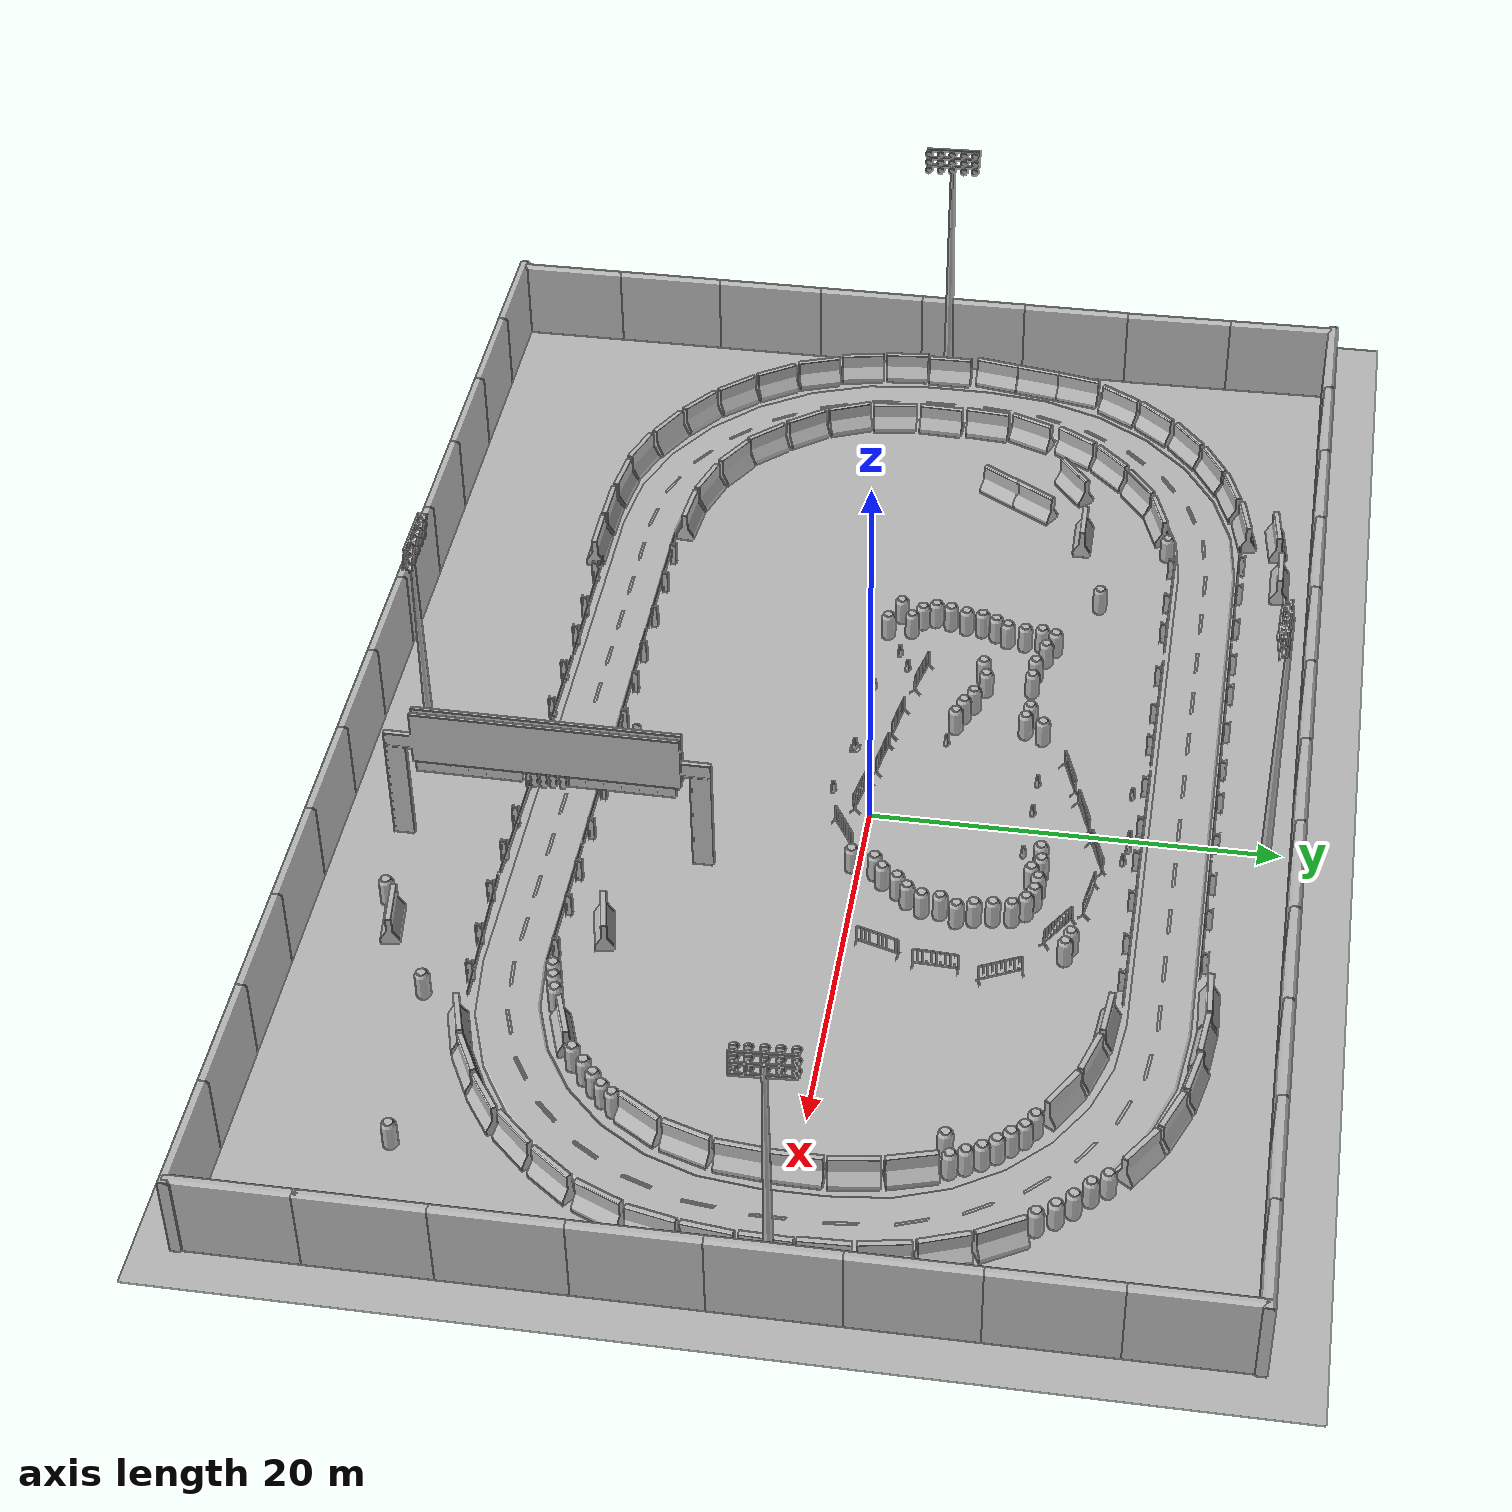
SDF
<sdf version="1.6">
 <world name="default">
  <model name="aws_robomaker_racetrack_Billboard_01">
   <static>true</static>
   <include><uri>model://aws_robomaker_racetrack_Billboard_01</uri></include>
   <pose>4.32789 -14.8431 -2e-06 0 1e-06 1.56416</pose>
  </model>
  <model name="aws_robomaker_racetrack_CrashworthBucket_01_00">
   <static>true</static>
   <include><uri>model://aws_robomaker_racetrack_CrashworthBucket_01</uri></include>
   <pose>-8.47522 4.09403 0.054 0 0 0</pose>
  </model>
  <model name="aws_robomaker_racetrack_CrashworthBucket_01_01">
   <static>true</static>
   <include><uri>model://aws_robomaker_racetrack_CrashworthBucket_01</uri></include>
   <pose>-7.67012 3.67698 0.054 0 0 0</pose>
  </model>
  <model name="aws_robomaker_racetrack_CrashworthBucket_01_02">
   <static>true</static>
   <include><uri>model://aws_robomaker_racetrack_CrashworthBucket_01</uri></include>
   <pose>-13.6708 -0.983538 0.054 0 0 0</pose>
  </model>
  <model name="aws_robomaker_racetrack_CrashworthBucket_01_03">
   <include><uri>model://aws_robomaker_racetrack_CrashworthBucket_01</uri></include>
   <pose>-13.6938 6.13266 0.054 0 0 0</pose>
  </model>
  <model name="aws_robomaker_racetrack_CrashworthBucket_01_04">
   <include><uri>model://aws_robomaker_racetrack_CrashworthBucket_01</uri></include>
   <pose>2.35672 8.58743 0.054 0 0 0.094608</pose>
  </model>
  <model name="aws_robomaker_racetrack_CrashworthBucket_01_05">
   <include><uri>model://aws_robomaker_racetrack_CrashworthBucket_01</uri></include>
   <pose>3.14399 8.69292 0 0 -0 0.292667</pose>
  </model>
  <model name="aws_robomaker_racetrack_CrashworthBucket_01_06">
   <include><uri>model://aws_robomaker_racetrack_CrashworthBucket_01</uri></include>
   <pose>5.18867 8.56895 0 0 0 -0.026658</pose>
  </model>
  <model name="aws_robomaker_racetrack_CrashworthBucket_01_07">
   <include><uri>model://aws_robomaker_racetrack_CrashworthBucket_01</uri></include>
   <pose>5.89383 8.24239 0.054 0 0 0</pose>
  </model>
  <model name="aws_robomaker_racetrack_CrashworthBucket_01_08">
   <include><uri>model://aws_robomaker_racetrack_CrashworthBucket_01</uri></include>
   <pose>8.58056 10.3426 0.054 0 0 0</pose>
  </model>
  <model name="aws_robomaker_racetrack_CrashworthBucket_01_09">
   <include><uri>model://aws_robomaker_racetrack_CrashworthBucket_01</uri></include>
   <pose>7.88227 10.5539 0.054 0 0 0</pose>
  </model>
  <model name="aws_robomaker_racetrack_CrashworthBucket_01_10">
   <include><uri>model://aws_robomaker_racetrack_CrashworthBucket_01</uri></include>
   <pose>22.2917 13.5697 0 0 -0 0</pose>
  </model>
  <model name="aws_robomaker_racetrack_CrashworthBucket_01_11">
   <include><uri>model://aws_robomaker_racetrack_CrashworthBucket_01</uri></include>
   <pose>22.9018 12.8693 0.054 0 0 0</pose>
  </model>
  <model name="aws_robomaker_racetrack_CrashworthBucket_01_12">
   <include><uri>model://aws_robomaker_racetrack_CrashworthBucket_01</uri></include>
   <pose>22.2128 6.62693 0.054 0 0 0</pose>
  </model>
  <model name="aws_robomaker_racetrack_CrashworthBucket_01_13">
   <include><uri>model://aws_robomaker_racetrack_CrashworthBucket_01</uri></include>
   <pose>20.9847 6.29253 0 0 -0 0</pose>
  </model>
  <model name="aws_robomaker_racetrack_CrashworthBucket_01_14">
   <include><uri>model://aws_robomaker_racetrack_CrashworthBucket_01</uri></include>
   <pose>24.073 -17.9303 0.054 0 0 0</pose>
  </model>
  <model name="aws_robomaker_racetrack_CrashworthBucket_01_15">
   <include><uri>model://aws_robomaker_racetrack_CrashworthBucket_01</uri></include>
   <pose>20.8422 -8.59507 0.054 0 0 0.012499</pose>
  </model>
  <model name="aws_robomaker_racetrack_CrashworthBucket_01_16">
   <include><uri>model://aws_robomaker_racetrack_CrashworthBucket_01</uri></include>
   <pose>20.3649 -9.17417 0 0 -0 0.004768</pose>
  </model>
  <model name="aws_robomaker_racetrack_CrashworthBucket_01_17">
   <include><uri>model://aws_robomaker_racetrack_CrashworthBucket_01</uri></include>
   <pose>19.7995 -9.67862 0.054 0 0 -0.003254</pose>
  </model>
  <model name="aws_robomaker_racetrack_CrashworthBucket_01_18">
   <include><uri>model://aws_robomaker_racetrack_CrashworthBucket_01</uri></include>
   <pose>19.1471 -10.2467 0.054 0 0 0</pose>
  </model>
  <model name="aws_robomaker_racetrack_CrashworthBucket_01_19">
   <include><uri>model://aws_robomaker_racetrack_CrashworthBucket_01</uri></include>
   <pose>18.3999 -10.9106 0.054 0 0 0</pose>
  </model>
  <model name="aws_robomaker_racetrack_CrashworthBucket_01_20">
   <include><uri>model://aws_robomaker_racetrack_CrashworthBucket_01</uri></include>
   <pose>-22.169 12.8311 0 0 -0 0</pose>
  </model>
  <model name="aws_robomaker_racetrack_CrashworthBucket_01_21">
   <include><uri>model://aws_robomaker_racetrack_CrashworthBucket_01</uri></include>
   <pose>-17.3216 9.66872 0.054 0 0 0</pose>
  </model>
  <model name="aws_robomaker_racetrack_CrashworthBucket_01_22">
   <include><uri>model://aws_robomaker_racetrack_CrashworthBucket_01</uri></include>
   <pose>14.1427 -12.6734 0.054 0 0 0</pose>
  </model>
  <model name="aws_robomaker_racetrack_CrashworthBucket_01_23">
   <include><uri>model://aws_robomaker_racetrack_CrashworthBucket_01</uri></include>
   <pose>14.9254 -12.4456 0.054 0 0 0</pose>
  </model>
  <model name="aws_robomaker_racetrack_CrashworthBucket_01_24">
   <include><uri>model://aws_robomaker_racetrack_CrashworthBucket_01</uri></include>
   <pose>-15.0558 -0.45872 0 0 -0 0</pose>
  </model>
  <model name="aws_robomaker_racetrack_CrashworthBucket_01_25">
   <include><uri>model://aws_robomaker_racetrack_CrashworthBucket_01</uri></include>
   <pose>13.3868 -12.8508 0.054 0 0 0</pose>
  </model>
  <model name="aws_robomaker_racetrack_CrashworthBucket_01_26">
   <include><uri>model://aws_robomaker_racetrack_CrashworthBucket_01</uri></include>
   <pose>9.22311 -21.8198 0.054 0 0 0</pose>
  </model>
  <model name="aws_robomaker_racetrack_CrashworthBucket_01_27">
   <include><uri>model://aws_robomaker_racetrack_CrashworthBucket_01</uri></include>
   <pose>3.82438 -0.358379 0 0 -0 0</pose>
  </model>
  <model name="aws_robomaker_racetrack_CrashworthBucket_01_28">
   <include><uri>model://aws_robomaker_racetrack_CrashworthBucket_01</uri></include>
   <pose>14.9648 -18.6736 0.054 0 0 0</pose>
  </model>
  <model name="aws_robomaker_racetrack_CrashworthBucket_01_29">
   <include><uri>model://aws_robomaker_racetrack_CrashworthBucket_01</uri></include>
   <pose>23.6827 12.1956 0.054 0 0 0</pose>
  </model>
  <model name="aws_robomaker_racetrack_CrashworthBucket_01_30">
   <include><uri>model://aws_robomaker_racetrack_CrashworthBucket_01</uri></include>
   <pose>24.3346 11.4874 0.054 0 0 0</pose>
  </model>
  <model name="aws_robomaker_racetrack_CrashworthBucket_01_31">
   <include><uri>model://aws_robomaker_racetrack_CrashworthBucket_01</uri></include>
   <pose>24.8882 10.6788 0.054 0 0 0</pose>
  </model>
  <model name="aws_robomaker_racetrack_CrashworthBucket_01_32">
   <include><uri>model://aws_robomaker_racetrack_CrashworthBucket_01</uri></include>
   <pose>20.5304 9.13561 0.054 0 0 -0.001449</pose>
  </model>
  <model name="aws_robomaker_racetrack_CrashworthBucket_01_33">
   <include><uri>model://aws_robomaker_racetrack_CrashworthBucket_01</uri></include>
   <pose>19.3714 10.0864 0.054 0 0 0</pose>
  </model>
  <model name="aws_robomaker_racetrack_CrashworthBucket_01_34">
   <include><uri>model://aws_robomaker_racetrack_CrashworthBucket_01</uri></include>
   <pose>20.0016 9.69426 0 0 0 -0.00182</pose>
  </model>
  <model name="aws_robomaker_racetrack_CrashworthBucket_01_35">
   <include><uri>model://aws_robomaker_racetrack_CrashworthBucket_01</uri></include>
   <pose>21.0478 8.57525 0.054 0 0 -0.000349</pose>
  </model>
  <model name="aws_robomaker_racetrack_CrashworthBucket_01_36">
   <include><uri>model://aws_robomaker_racetrack_CrashworthBucket_01</uri></include>
   <pose>21.5218 7.97169 0.054 0 0 0</pose>
  </model>
  <model name="aws_robomaker_racetrack_CrashworthBucket_01_37">
   <include><uri>model://aws_robomaker_racetrack_CrashworthBucket_01</uri></include>
   <pose>21.8874 7.29413 0.054 0 0 0</pose>
  </model>
  <model name="aws_robomaker_racetrack_CrashworthBucket_01_38">
   <include><uri>model://aws_robomaker_racetrack_CrashworthBucket_01</uri></include>
   <pose>6.38383 7.63289 0.054 0 0 0</pose>
  </model>
  <model name="aws_robomaker_racetrack_CrashworthBucket_01_39">
   <include><uri>model://aws_robomaker_racetrack_CrashworthBucket_01</uri></include>
   <pose>6.48514 6.73841 0.054 0 0 0</pose>
  </model>
  <model name="aws_robomaker_racetrack_CrashworthBucket_01_40">
   <include><uri>model://aws_robomaker_racetrack_CrashworthBucket_01</uri></include>
   <pose>6.63137 5.86016 0.054 0 0 0</pose>
  </model>
  <model name="aws_robomaker_racetrack_CrashworthBucket_01_41">
   <include><uri>model://aws_robomaker_racetrack_CrashworthBucket_01</uri></include>
   <pose>6.84089 5.04433 0.054 0 0 0</pose>
  </model>
  <model name="aws_robomaker_racetrack_CrashworthBucket_01_42">
   <include><uri>model://aws_robomaker_racetrack_CrashworthBucket_01</uri></include>
   <pose>6.41586 4.22597 0.054 0 0 0</pose>
  </model>
  <model name="aws_robomaker_racetrack_CrashworthBucket_01_43">
   <include><uri>model://aws_robomaker_racetrack_CrashworthBucket_01</uri></include>
   <pose>4.45229 8.66174 0.054 0 0 0.095583</pose>
  </model>
  <model name="aws_robomaker_racetrack_CrashworthBucket_01_44">
   <include><uri>model://aws_robomaker_racetrack_CrashworthBucket_01</uri></include>
   <pose>-13.8311 5.21601 0.054 0 0 0</pose>
  </model>
  <model name="aws_robomaker_racetrack_CrashworthBucket_01_45">
   <include><uri>model://aws_robomaker_racetrack_CrashworthBucket_01</uri></include>
   <pose>5.3642 2.03973 0.054 0 0 -0.008872</pose>
  </model>
  <model name="aws_robomaker_racetrack_CrashworthBucket_01_46">
   <include><uri>model://aws_robomaker_racetrack_CrashworthBucket_01</uri></include>
   <pose>5.91311 2.58362 0 0 0 -0.010849</pose>
  </model>
  <model name="aws_robomaker_racetrack_CrashworthBucket_01_47">
   <include><uri>model://aws_robomaker_racetrack_CrashworthBucket_01</uri></include>
   <pose>6.38729 3.3437 0.054 0 0 0</pose>
  </model>
  <model name="aws_robomaker_racetrack_CrashworthBucket_01_48">
   <include><uri>model://aws_robomaker_racetrack_CrashworthBucket_01</uri></include>
   <pose>4.78436 1.25544 0 0 0 -0.004687</pose>
  </model>
  <model name="aws_robomaker_racetrack_CrashworthBucket_01_49">
   <include><uri>model://aws_robomaker_racetrack_CrashworthBucket_01</uri></include>
   <pose>4.1948 0.806848 0.054 0 0 -0.002707</pose>
  </model>
  <model name="aws_robomaker_racetrack_CrashworthBucket_01_50">
   <include><uri>model://aws_robomaker_racetrack_CrashworthBucket_01</uri></include>
   <pose>-6.80733 3.36416 0.054 0 0 0</pose>
  </model>
  <model name="aws_robomaker_racetrack_CrashworthBucket_01_51">
   <include><uri>model://aws_robomaker_racetrack_CrashworthBucket_01</uri></include>
   <pose>-9.83411 4.55632 0.054 0 0 0</pose>
  </model>
  <model name="aws_robomaker_racetrack_CrashworthBucket_01_52">
   <include><uri>model://aws_robomaker_racetrack_CrashworthBucket_01</uri></include>
   <pose>-10.8194 4.31922 0.054 0 0 0</pose>
  </model>
  <model name="aws_robomaker_racetrack_CrashworthBucket_01_53">
   <include><uri>model://aws_robomaker_racetrack_CrashworthBucket_01</uri></include>
   <pose>3.7947 8.27498 0 0 0 -0.244875</pose>
  </model>
  <model name="aws_robomaker_racetrack_CrashworthBucket_01_54">
   <include><uri>model://aws_robomaker_racetrack_CrashworthBucket_01</uri></include>
   <pose>-10.1026 6.87186 0.054 0 0 0</pose>
  </model>
  <model name="aws_robomaker_racetrack_CrashworthBucket_01_55">
   <include><uri>model://aws_robomaker_racetrack_CrashworthBucket_01</uri></include>
   <pose>-11.2375 6.93335 0.054 0 0 0</pose>
  </model>
  <model name="aws_robomaker_racetrack_CrashworthBucket_01_56">
   <include><uri>model://aws_robomaker_racetrack_CrashworthBucket_01</uri></include>
   <pose>-13.9209 0.216601 0.054 0 0 0</pose>
  </model>
  <model name="aws_robomaker_racetrack_CrashworthBucket_01_57">
   <include><uri>model://aws_robomaker_racetrack_CrashworthBucket_01</uri></include>
   <pose>-7.72969 7.02543 0.054 0 0 0</pose>
  </model>
  <model name="aws_robomaker_racetrack_CrashworthBucket_01_58">
   <include><uri>model://aws_robomaker_racetrack_CrashworthBucket_01</uri></include>
   <pose>-6.91293 6.87432 0.054 0 0 0</pose>
  </model>
  <model name="aws_robomaker_racetrack_CrashworthBucket_01_59">
   <include><uri>model://aws_robomaker_racetrack_CrashworthBucket_01</uri></include>
   <pose>-6.56208 7.77782 0.054 0 0 0</pose>
  </model>
  <model name="aws_robomaker_racetrack_CrashworthBucket_01_60">
   <include><uri>model://aws_robomaker_racetrack_CrashworthBucket_01</uri></include>
   <pose>-14.6963 0.705029 0 0 -0 0.00632</pose>
  </model>
  <model name="aws_robomaker_racetrack_CrashworthBucket_01_61">
   <include><uri>model://aws_robomaker_racetrack_CrashworthBucket_01</uri></include>
   <pose>-14.205 4.57376 0.054 0 0 0</pose>
  </model>
  <model name="aws_robomaker_racetrack_CrashworthBucket_01_62">
   <include><uri>model://aws_robomaker_racetrack_CrashworthBucket_01</uri></include>
   <pose>-14.8093 2.14739 0.054 0 0 0</pose>
  </model>
  <model name="aws_robomaker_racetrack_CrashworthBucket_01_63">
   <include><uri>model://aws_robomaker_racetrack_CrashworthBucket_01</uri></include>
   <pose>-14.964 1.3691 0.054 0 0 0.003001</pose>
  </model>
  <model name="aws_robomaker_racetrack_CrashworthBucket_01_64">
   <include><uri>model://aws_robomaker_racetrack_CrashworthBucket_01</uri></include>
   <pose>-14.5066 3.82709 0.054 0 0 -0.127634</pose>
  </model>
  <model name="aws_robomaker_racetrack_CrashworthBucket_01_65">
   <include><uri>model://aws_robomaker_racetrack_CrashworthBucket_01</uri></include>
   <pose>-14.5756 2.99063 0.054 0 0 0</pose>
  </model>
  <model name="aws_robomaker_racetrack_CrashworthBucket_01_66">
   <include><uri>model://aws_robomaker_racetrack_CrashworthBucket_01</uri></include>
   <pose>-13.7254 7.00826 0.054 0 0 0</pose>
  </model>
  <model name="aws_robomaker_racetrack_CrashworthBucket_01_67">
   <include><uri>model://aws_robomaker_racetrack_CrashworthBucket_01</uri></include>
   <pose>-13.4797 7.73167 0.054 0 0 0</pose>
  </model>
  <model name="aws_robomaker_racetrack_CrashworthBucket_01_68">
   <include><uri>model://aws_robomaker_racetrack_CrashworthBucket_01</uri></include>
   <pose>-12.5612 7.3288 0.054 0 0 0</pose>
  </model>
  <model name="aws_robomaker_racetrack_FenceMesh_01_00">
   <include><uri>model://aws_robomaker_racetrack_FenceMesh_01</uri></include>
   <pose>4.2331 -11.1761 5.05223 0 0 -0.006038</pose>
  </model>
  <model name="aws_robomaker_racetrack_FenceMesh_01_01">
   <include><uri>model://aws_robomaker_racetrack_FenceMesh_01</uri></include>
   <pose>4.16406 -18.6269 5.05223 0 0 -0.006038</pose>
  </model>
  <model name="aws_robomaker_racetrack_FenceMesh_01_02">
   <include><uri>model://aws_robomaker_racetrack_FenceMesh_01</uri></include>
   <pose>4.63223 -18.6067 5.05223 0 0 -0.006038</pose>
  </model>
  <model name="aws_robomaker_racetrack_FenceMesh_01_03">
   <include><uri>model://aws_robomaker_racetrack_FenceMesh_01</uri></include>
   <pose>4.67467 -11.1966 5.05223 0 0 -0.006038</pose>
  </model>
  <model name="aws_robomaker_racetrack_Fence_01_00">
   <include><uri>model://aws_robomaker_racetrack_Fence_01</uri></include>
   <pose>7.552996 13.158695 0 0 0 -1.57272</pose>
  </model>
  <model name="aws_robomaker_racetrack_Fence_01_01">
   <include><uri>model://aws_robomaker_racetrack_Fence_01</uri></include>
   <pose>-0.500271 13.158695 0 0 0 -1.57272</pose>
  </model>
  <model name="aws_robomaker_racetrack_Fence_01_02">
   <include><uri>model://aws_robomaker_racetrack_Fence_01</uri></include>
   <pose>-8.897229 13.158695 0 0 0 -1.57272</pose>
  </model>
  <model name="aws_robomaker_racetrack_Fence_01_03">
   <include><uri>model://aws_robomaker_racetrack_Fence_01</uri></include>
   <pose>-17.681196 13.158695 0 0 0 -1.57272</pose>
  </model>
  <model name="aws_robomaker_racetrack_Fence_01_04">
   <include><uri>model://aws_robomaker_racetrack_Fence_01</uri></include>
   <pose>-12.990376 -16.857170 0.054 -0.0 0.0 -1.558614</pose>
  </model>
  <model name="aws_robomaker_racetrack_Fence_01_05">
   <include><uri>model://aws_robomaker_racetrack_Fence_01</uri></include>
   <pose>-4.880881 -16.849474 0.054  0 0 -1.572721</pose>
  </model>
  <model name="aws_robomaker_racetrack_Fence_01_06">
   <include><uri>model://aws_robomaker_racetrack_Fence_01</uri></include>
   <pose>3.247635 -16.899557 0.054  0 0 -1.581650</pose>
  </model>
  <model name="aws_robomaker_racetrack_Fence_01_07">
   <include><uri>model://aws_robomaker_racetrack_Fence_01</uri></include>
   <pose>11.364270 -16.813890 0.054  0.0 0.0 -1.525504</pose>
  </model>
  <model name="aws_robomaker_racetrack_Fence_01_08">
   <include><uri>model://aws_robomaker_racetrack_Fence_01</uri></include>
   <pose>-15.529042 -13.134610 0.054 0 -0 1.57158</pose>
  </model>
  <model name="aws_robomaker_racetrack_Fence_01_09">
   <include><uri>model://aws_robomaker_racetrack_Fence_01</uri></include>
   <pose>-7.391050 -13.134610 0.054651 0 0.0 1.580400</pose>
  </model>
  <model name="aws_robomaker_racetrack_Fence_01_10">
   <include><uri>model://aws_robomaker_racetrack_Fence_01</uri></include>
   <pose>0.720398 -13.134610 0.054671 0 -0 1.57158</pose>
  </model>
  <model name="aws_robomaker_racetrack_Fence_01_11">
   <include><uri>model://aws_robomaker_racetrack_Fence_01</uri></include>
   <pose>8.89898 -13.134610 0.054638 0.0 0.0 1.572679</pose>
  </model>
  <model name="aws_robomaker_racetrack_Fence_01_12">
   <include><uri>model://aws_robomaker_racetrack_Fence_01</uri></include>
   <pose>-18.882746 16.818918 0.054  0 -0 1.57158</pose>
  </model>
  <model name="aws_robomaker_racetrack_Fence_01_13">
   <include><uri>model://aws_robomaker_racetrack_Fence_01</uri></include>
   <pose>-10.776134 16.818918 0.054  0 -0 1.57158</pose>
  </model>
  <model name="aws_robomaker_racetrack_Fence_01_14">
   <include><uri>model://aws_robomaker_racetrack_Fence_01</uri></include>
   <pose>-2.679413 16.818918 0 0 -0 1.57158</pose>
  </model>
  <model name="aws_robomaker_racetrack_Fence_01_15">
   <include><uri>model://aws_robomaker_racetrack_Fence_01</uri></include>
   <pose>5.475008 16.818918 0.054  0 -0 1.57158</pose>
  </model>
  <model name="aws_robomaker_racetrack_Fence_02_00">
   <include><uri>model://aws_robomaker_racetrack_Fence_02</uri></include>
   <pose>-1.05264 -0.5238 0.040535 -0.008781 0.086261 -1.77545</pose>
  </model>
  <model name="aws_robomaker_racetrack_Fence_02_01">
   <include><uri>model://aws_robomaker_racetrack_Fence_02</uri></include>
   <pose>9.06357 1.626 0 0 0 -0.300407</pose>
  </model>
  <model name="aws_robomaker_racetrack_Fence_02_02">
   <include><uri>model://aws_robomaker_racetrack_Fence_02</uri></include>
   <pose>-3.88076 0.08215 0 0 0 -1.73608</pose>
  </model>
  <model name="aws_robomaker_racetrack_Fence_02_03">
   <include><uri>model://aws_robomaker_racetrack_Fence_02</uri></include>
   <pose>-6.69129 0.495608 0 0 0 -1.73608</pose>
  </model>
  <model name="aws_robomaker_racetrack_Fence_02_04">
   <include><uri>model://aws_robomaker_racetrack_Fence_02</uri></include>
   <pose>-10.283561 1.223148 0.054 0 0 -1.789875</pose>
  </model>
  <model name="aws_robomaker_racetrack_Fence_02_05">
   <include><uri>model://aws_robomaker_racetrack_Fence_02</uri></include>
   <pose>4.57205 11.1353 0 0 0 -1.73608</pose>
  </model>
  <model name="aws_robomaker_racetrack_Fence_02_06">
   <include><uri>model://aws_robomaker_racetrack_Fence_02</uri></include>
   <pose>6.8958583 9.887979 0 0 0 -2.140475</pose>
  </model>
  <model name="aws_robomaker_racetrack_Fence_02_07">
   <include><uri>model://aws_robomaker_racetrack_Fence_02</uri></include>
   <pose>1.60246 11.2143 0 0 -0 1.90339</pose>
  </model>
  <model name="aws_robomaker_racetrack_Fence_02_08">
   <include><uri>model://aws_robomaker_racetrack_Fence_02</uri></include>
   <pose>-1.13 10.3272 0 0 -0 1.90339</pose>
  </model>
  <model name="aws_robomaker_racetrack_Fence_02_09">
   <include><uri>model://aws_robomaker_racetrack_Fence_02</uri></include>
   <pose>-3.85384 9.39461 0 0 -0 1.90339</pose>
  </model>
  <model name="aws_robomaker_racetrack_Fence_02_10">
   <include><uri>model://aws_robomaker_racetrack_Fence_02</uri></include>
   <pose>9.89165 4.45225 0 0 0 -0.045392</pose>
  </model>
  <model name="aws_robomaker_racetrack_Fence_02_11">
   <include><uri>model://aws_robomaker_racetrack_Fence_02</uri></include>
   <pose>10.0686 7.48939 0 0 -0 0.450699</pose>
  </model>
  <model name="aws_robomaker_racetrack_Fence_02_12">
   <include><uri>model://aws_robomaker_racetrack_Fence_02</uri></include>
   <pose>1.65856 -1.03383 0 0 0 -1.02955</pose>
  </model>
  <model name="aws_robomaker_racetrack_RaceStartLight_01_00">
   <include><uri>model://aws_robomaker_racetrack_RaceStartLight_01</uri></include>
   <pose>4.13359 -14.1692 5.08709 0 -0 0</pose>
  </model>
  <model name="aws_robomaker_racetrack_RaceStartLight_01_01">
   <include><uri>model://aws_robomaker_racetrack_RaceStartLight_01</uri></include>
   <pose>4.14665 -14.6522 5.08709 0 -0 0</pose>
  </model>
  <model name="aws_robomaker_racetrack_RaceStartLight_01_02">
   <include><uri>model://aws_robomaker_racetrack_RaceStartLight_01</uri></include>
   <pose>4.21676 -15.0918 5.08709 0 -0 0</pose>
  </model>
  <model name="aws_robomaker_racetrack_RaceStartLight_01_03">
   <include><uri>model://aws_robomaker_racetrack_RaceStartLight_01</uri></include>
   <pose>4.17594 -15.5526 5.08709 0 -0 0</pose>
  </model>
  <model name="aws_robomaker_racetrack_StonePier_01_00">
   <include><uri>model://aws_robomaker_racetrack_StonePier_01</uri></include>
   <pose>-21.1732 -12.7799 0.054 0 -0 -0.086667</pose>
  </model>
  <model name="aws_robomaker_racetrack_StonePier_01_01">
   <include><uri>model://aws_robomaker_racetrack_StonePier_01</uri></include>
   <pose>-23.6727 -12.2854 0.054 0 -0.0 -0.301631</pose>
  </model>
  <model name="aws_robomaker_racetrack_StonePier_01_02">
   <include><uri>model://aws_robomaker_racetrack_StonePier_01</uri></include>
   <pose>-22.8128 8.293 0.054 0 -0 0.009742</pose>
  </model>
  <model name="aws_robomaker_racetrack_StonePier_01_03">
   <include><uri>model://aws_robomaker_racetrack_StonePier_01</uri></include>
   <pose>-24.2891 12.2118 0.054 0 -0 0.334226</pose>
  </model>
  <model name="aws_robomaker_racetrack_StonePier_01_04">
   <include><uri>model://aws_robomaker_racetrack_StonePier_01</uri></include>
   <pose>-20.3219 18.8912 0.054 0 -0.0 0.009742</pose>
  </model>
  <model name="aws_robomaker_racetrack_StonePier_01_05">
   <include><uri>model://aws_robomaker_racetrack_StonePier_01</uri></include>
   <pose>11.0892 17.2043 0.054 0 -0.0 0.029389</pose>
  </model>
  <model name="aws_robomaker_racetrack_StonePier_01_06">
   <include><uri>model://aws_robomaker_racetrack_StonePier_01</uri></include>
   <pose>13.5633 17.1121 0.054 0 -0.0 -0.108086</pose>
  </model>
  <model name="aws_robomaker_racetrack_StonePier_01_07">
   <include><uri>model://aws_robomaker_racetrack_StonePier_01</uri></include>
   <pose>16.0013 16.8104 0.054 0 -0.0 -0.206147</pose>
  </model>
  <model name="aws_robomaker_racetrack_StonePier_01_08">
   <include><uri>model://aws_robomaker_racetrack_StonePier_01</uri></include>
   <pose>18.4263 16.0384 0.054 0 -0.0 -0.379591</pose>
  </model>
  <model name="aws_robomaker_racetrack_StonePier_01_09">
   <include><uri>model://aws_robomaker_racetrack_StonePier_01</uri></include>
   <pose>17.8323 11.1467 0.054 0 -0.0 -0.536699</pose>
  </model>
  <model name="aws_robomaker_racetrack_StonePier_01_10">
   <include><uri>model://aws_robomaker_racetrack_StonePier_01</uri></include>
   <pose>22.7563 5.03589 0.054 0 -0.0 -1.28348</pose>
  </model>
  <model name="aws_robomaker_racetrack_StonePier_01_11">
   <include><uri>model://aws_robomaker_racetrack_StonePier_01</uri></include>
   <pose>23.2964 2.57509 0.054 -0 -0.0 -1.43498</pose>
  </model>
  <model name="aws_robomaker_racetrack_StonePier_01_12">
   <include><uri>model://aws_robomaker_racetrack_StonePier_01</uri></include>
   <pose>23.4326 0.10745 0.054 -0 -0.0 -1.58404</pose>
  </model>
  <model name="aws_robomaker_racetrack_StonePier_01_13">
   <include><uri>model://aws_robomaker_racetrack_StonePier_01</uri></include>
   <pose>23.2774 -2.40527 0.054 0 -0.0 -1.65922</pose>
  </model>
  <model name="aws_robomaker_racetrack_StonePier_01_14">
   <include><uri>model://aws_robomaker_racetrack_StonePier_01</uri></include>
   <pose>22.705 -4.89186 0.054 -0 -0.0 -1.88566</pose>
  </model>
  <model name="aws_robomaker_racetrack_StonePier_01_15">
   <include><uri>model://aws_robomaker_racetrack_StonePier_01</uri></include>
   <pose>21.6688 -7.19526 0.054 0 -0.0 -2.13625</pose>
  </model>
  <model name="aws_robomaker_racetrack_StonePier_01_16">
   <include><uri>model://aws_robomaker_racetrack_StonePier_01</uri></include>
   <pose>28.1211 -0.475719 0.054 0 -0.0 -1.59506</pose>
  </model>
  <model name="aws_robomaker_racetrack_StonePier_01_17">
   <include><uri>model://aws_robomaker_racetrack_StonePier_01</uri></include>
   <pose>16.7061 -11.7058 0.054 -0 -0.0 -2.7953</pose>
  </model>
  <model name="aws_robomaker_racetrack_StonePier_01_18">
   <include><uri>model://aws_robomaker_racetrack_StonePier_01</uri></include>
   <pose>28.0027 -3.03906 0.054 0 -0.0 -1.68291</pose>
  </model>
  <model name="aws_robomaker_racetrack_StonePier_01_19">
   <include><uri>model://aws_robomaker_racetrack_StonePier_01</uri></include>
   <pose>9.84486 -11.2119 0.054 0 -0.0 -2.93657</pose>
  </model>
  <model name="aws_robomaker_racetrack_StonePier_01_20">
   <include><uri>model://aws_robomaker_racetrack_StonePier_01</uri></include>
   <pose>10.8625 -21.1556 0.054 -0 -0.0 0.135159</pose>
  </model>
  <model name="aws_robomaker_racetrack_StonePier_01_21">
   <include><uri>model://aws_robomaker_racetrack_StonePier_01</uri></include>
   <pose>17.2914 -16.4156 0.054 0 -0.0 0.298911</pose>
  </model>
  <model name="aws_robomaker_racetrack_StonePier_01_22">
   <include><uri>model://aws_robomaker_racetrack_StonePier_01</uri></include>
   <pose>19.6208 -15.4615 0.054 0 -0.0 0.489077</pose>
  </model>
  <model name="aws_robomaker_racetrack_StonePier_01_23">
   <include><uri>model://aws_robomaker_racetrack_StonePier_01</uri></include>
   <pose>21.7939 -14.1476 0.054 0 -0.0 0.61668</pose>
  </model>
  <model name="aws_robomaker_racetrack_StonePier_01_24">
   <include><uri>model://aws_robomaker_racetrack_StonePier_01</uri></include>
   <pose>23.6698 -12.3608 0.054 0 -0.0 0.810318</pose>
  </model>
  <model name="aws_robomaker_racetrack_StonePier_01_25">
   <include><uri>model://aws_robomaker_racetrack_StonePier_01</uri></include>
   <pose>25.3929 -10.3347 0.054 -0 -0.0 0.931507</pose>
  </model>
  <model name="aws_robomaker_racetrack_StonePier_01_26">
   <include><uri>model://aws_robomaker_racetrack_StonePier_01</uri></include>
   <pose>27.7466 4.53211 0.054 0 -0.0 1.75246</pose>
  </model>
  <model name="aws_robomaker_racetrack_StonePier_01_27">
   <include><uri>model://aws_robomaker_racetrack_StonePier_01</uri></include>
   <pose>27.0691 6.99271 0.054 0 -0.0 1.91654</pose>
  </model>
  <model name="aws_robomaker_racetrack_StonePier_01_28">
   <include><uri>model://aws_robomaker_racetrack_StonePier_01</uri></include>
   <pose>26.0366 9.29805 0.054 0 -0.0 2.08782</pose>
  </model>
  <model name="aws_robomaker_racetrack_StonePier_01_29">
   <include><uri>model://aws_robomaker_racetrack_StonePier_01</uri></include>
   <pose>26.7385 -7.99231 0.054 -0 -0.0 1.16098</pose>
  </model>
  <model name="aws_robomaker_racetrack_StonePier_01_30">
   <include><uri>model://aws_robomaker_racetrack_StonePier_01</uri></include>
   <pose>27.5962 -5.54706 0.054 0 -0.0 1.36231</pose>
  </model>
  <model name="aws_robomaker_racetrack_StonePier_01_31">
   <include><uri>model://aws_robomaker_racetrack_StonePier_01</uri></include>
   <pose>28.0314 1.9989 0.054 0 -0.0 -1.53351</pose>
  </model>
  <model name="aws_robomaker_racetrack_StonePier_01_32">
   <include><uri>model://aws_robomaker_racetrack_StonePier_01</uri></include>
   <pose>20.6714 14.8473 0.054 0 -0.0 -0.587598</pose>
  </model>
  <model name="aws_robomaker_racetrack_StonePier_01_33">
   <include><uri>model://aws_robomaker_racetrack_StonePier_01</uri></include>
   <pose>12.9654 12.6879 0.054 0 -0.0 -0.096781</pose>
  </model>
  <model name="aws_robomaker_racetrack_StonePier_01_34">
   <include><uri>model://aws_robomaker_racetrack_StonePier_01</uri></include>
   <pose>15.5357 12.1477 0.054 -0 0.00036 -0.29956</pose>
  </model>
  <model name="aws_robomaker_racetrack_StonePier_01_35">
   <include><uri>model://aws_robomaker_racetrack_StonePier_01</uri></include>
   <pose>-23.832 18.561 0.054 -0 -0.0 0.133251</pose>
  </model>
  <model name="aws_robomaker_racetrack_StonePier_01_36">
   <include><uri>model://aws_robomaker_racetrack_StonePier_01</uri></include>
   <pose>-26.5946 11.0295 0.054 0 0.00036 0.646791</pose>
  </model>
  <model name="aws_robomaker_racetrack_StonePier_01_37">
   <include><uri>model://aws_robomaker_racetrack_StonePier_01</uri></include>
   <pose>-24.4271 16.8105 0.054 -0 -0.0 0.217772</pose>
  </model>
  <model name="aws_robomaker_racetrack_StonePier_01_38">
   <include><uri>model://aws_robomaker_racetrack_StonePier_01</uri></include>
   <pose>-28.6752 9.30494 0.054 0 -0.0 0.789682</pose>
  </model>
  <model name="aws_robomaker_racetrack_StonePier_01_39">
   <include><uri>model://aws_robomaker_racetrack_StonePier_01</uri></include>
   <pose>-30.2584 7.24451 0.054 -0 -0.0 1.02306</pose>
  </model>
  <model name="aws_robomaker_racetrack_StonePier_01_40">
   <include><uri>model://aws_robomaker_racetrack_StonePier_01</uri></include>
   <pose>-18.3212 -17.1986 0.054 0 -0.0 -0.000165</pose>
  </model>
  <model name="aws_robomaker_racetrack_StonePier_01_41">
   <include><uri>model://aws_robomaker_racetrack_StonePier_01</uri></include>
   <pose>-26.1157 -11.2238 0.054 0 -0.0 -0.528829</pose>
  </model>
  <model name="aws_robomaker_racetrack_StonePier_01_42">
   <include><uri>model://aws_robomaker_racetrack_StonePier_01</uri></include>
   <pose>-28.1466 -9.75745 0.054 0 -0.0 -0.811127</pose>
  </model>
  <model name="aws_robomaker_racetrack_StonePier_01_43">
   <include><uri>model://aws_robomaker_racetrack_StonePier_01</uri></include>
   <pose>-29.8572 -7.79098 0.054 0 -0.0 -0.924577</pose>
  </model>
  <model name="aws_robomaker_racetrack_StonePier_01_44">
   <include><uri>model://aws_robomaker_racetrack_StonePier_01</uri></include>
   <pose>-31.1336 -5.56451 0.054 0 -0.0 -1.16956</pose>
  </model>
  <model name="aws_robomaker_racetrack_StonePier_01_45">
   <include><uri>model://aws_robomaker_racetrack_StonePier_01</uri></include>
   <pose>-31.6395 -3.07904 0.054 -0 -0.0 -1.43795</pose>
  </model>
  <model name="aws_robomaker_racetrack_StonePier_01_46">
   <include><uri>model://aws_robomaker_racetrack_StonePier_01</uri></include>
   <pose>-31.7709 -0.48849 0.054 0 -0.0 -1.61074</pose>
  </model>
  <model name="aws_robomaker_racetrack_StonePier_01_47">
   <include><uri>model://aws_robomaker_racetrack_StonePier_01</uri></include>
   <pose>-31.7363 2.12666 0.054 0 -0.0 -1.64853</pose>
  </model>
  <model name="aws_robomaker_racetrack_StonePier_01_48">
   <include><uri>model://aws_robomaker_racetrack_StonePier_01</uri></include>
   <pose>-31.2901 4.63965 0.054 -0 -0.0 -1.9545</pose>
  </model>
  <model name="aws_robomaker_racetrack_StonePier_01_49">
   <include><uri>model://aws_robomaker_racetrack_StonePier_01</uri></include>
   <pose>-25.0833 5.46077 -2.5e-05 2e-06 -2e-05 -2.1191</pose>
  </model>
  <model name="aws_robomaker_racetrack_StonePier_01_50">
   <include><uri>model://aws_robomaker_racetrack_StonePier_01</uri></include>
   <pose>-26.2415 3.56444 -3.6e-05 1e-06 -2.8e-05 -2.1191</pose>
  </model>
  <model name="aws_robomaker_racetrack_StonePier_01_51">
   <include><uri>model://aws_robomaker_racetrack_StonePier_01</uri></include>
   <pose>-27.0954 7.40849 0.054 -0 0.00036 -2.46174</pose>
  </model>
  <model name="aws_robomaker_racetrack_StonePier_01_52">
   <include><uri>model://aws_robomaker_racetrack_StonePier_01</uri></include>
   <pose>-28.2666 -15.3279 0.054 0 0.00036 -0.483595</pose>
  </model>
  <model name="aws_robomaker_racetrack_StonePier_01_53">
   <include><uri>model://aws_robomaker_racetrack_StonePier_01</uri></include>
   <pose>-30.4813 -13.931 0.054 0 -0.0 2.50624</pose>
  </model>
  <model name="aws_robomaker_racetrack_StonePier_01_54">
   <include><uri>model://aws_robomaker_racetrack_StonePier_01</uri></include>
   <pose>-32.3931 -12.181 0.054 0 -0.0 2.30053</pose>
  </model>
  <model name="aws_robomaker_racetrack_StonePier_01_55">
   <include><uri>model://aws_robomaker_racetrack_StonePier_01</uri></include>
   <pose>-33.9725 -10.1825 0.054 0 -0.0 2.15404</pose>
  </model>
  <model name="aws_robomaker_racetrack_StonePier_01_56">
   <include><uri>model://aws_robomaker_racetrack_StonePier_01</uri></include>
   <pose>-35.2144 -7.92381 0.054 0 -0.0 1.91826</pose>
  </model>
  <model name="aws_robomaker_racetrack_StonePier_01_57">
   <include><uri>model://aws_robomaker_racetrack_StonePier_01</uri></include>
   <pose>-36.4999 -3.03273 0.054 -0 0.00036 -1.47965</pose>
  </model>
  <model name="aws_robomaker_racetrack_StonePier_01_58">
   <include><uri>model://aws_robomaker_racetrack_StonePier_01</uri></include>
   <pose>-36.5369 -0.578473 -0.000468 -0 0.000348 1.59189</pose>
  </model>
  <model name="aws_robomaker_racetrack_StonePier_01_59">
   <include><uri>model://aws_robomaker_racetrack_StonePier_01</uri></include>
   <pose>-36.0789 -5.53149 0.054 0 -0.0 1.76121</pose>
  </model>
  <model name="aws_robomaker_racetrack_StonePier_01_60">
   <include><uri>model://aws_robomaker_racetrack_StonePier_01</uri></include>
   <pose>-36.5742 2.13483 -4.9e-05 -4.8e-05 -6.2e-05 1.40891</pose>
  </model>
  <model name="aws_robomaker_racetrack_StonePier_01_61">
   <include><uri>model://aws_robomaker_racetrack_StonePier_01</uri></include>
   <pose>-36.1891 4.48288 0.000698 -7e-05 -0.000662 1.40758</pose>
  </model>
  <model name="aws_robomaker_racetrack_StonePier_01_62">
   <include><uri>model://aws_robomaker_racetrack_StonePier_01</uri></include>
   <pose>-35.7706 6.79941 0.00067 5.5e-05 0.000534 1.37633</pose>
  </model>
  <model name="aws_robomaker_racetrack_StonePier_01_63">
   <include><uri>model://aws_robomaker_racetrack_StonePier_01</uri></include>
   <pose>-34.5101 9.28526 0.054 0 -0.0 1.03684</pose>
  </model>
  <model name="aws_robomaker_racetrack_StonePier_01_64">
   <include><uri>model://aws_robomaker_racetrack_StonePier_01</uri></include>
   <pose>-33.1083 11.4014 0.054 0 -0.0 0.877747</pose>
  </model>
  <model name="aws_robomaker_racetrack_StonePier_01_65">
   <include><uri>model://aws_robomaker_racetrack_StonePier_01</uri></include>
   <pose>-31.2882 13.312 0.054 -0 -0.0 0.701782</pose>
  </model>
  <model name="aws_robomaker_racetrack_StonePier_01_66">
   <include><uri>model://aws_robomaker_racetrack_StonePier_01</uri></include>
   <pose>-29.1909 14.829 0.054 0 -0.0 0.529025</pose>
  </model>
  <model name="aws_robomaker_racetrack_StonePier_01_67">
   <include><uri>model://aws_robomaker_racetrack_StonePier_01</uri></include>
   <pose>-26.9181 15.9588 0.054 0 -0.0 0.349577</pose>
  </model>
  <model name="aws_robomaker_racetrack_StonePier_01_68">
   <include><uri>model://aws_robomaker_racetrack_StonePier_01</uri></include>
   <pose>-20.8526 -17.1365 0.054 -0 0.00036 -0.016586</pose>
  </model>
  <model name="aws_robomaker_racetrack_StonePier_01_69">
   <include><uri>model://aws_robomaker_racetrack_StonePier_01</uri></include>
   <pose>-23.3756 -16.9024 0.054 0 -0.0 -0.119704</pose>
  </model>
  <model name="aws_robomaker_racetrack_StonePier_01_70">
   <include><uri>model://aws_robomaker_racetrack_StonePier_01</uri></include>
   <pose>-25.8909 -16.4126 0.054 0 -0.0 -0.32217</pose>
  </model>
  <model name="aws_robomaker_racetrack_StopSign_01_00">
   <include><uri>model://aws_robomaker_racetrack_StopSign_01</uri></include>
   <pose>-2.7487 -12.1054 0.000775 0.075944 0.005053 -1.56731</pose>
  </model>
  <model name="aws_robomaker_racetrack_Track_05_00">
   <include><uri>model://aws_robomaker_racetrack_Track_05</uri></include>
   <pose>0 0 0.051 0 -0 0</pose>
  </model>
  <model name="aws_robomaker_racetrack_Trackline_01_00">
   <include><uri>model://aws_robomaker_racetrack_Trackline_01</uri></include>
   <pose>-4.24539 0 0.102 0 -0 0</pose>
  </model>
  <model name="aws_robomaker_racetrack_TrafficCone_01_00">
   <include><uri>model://aws_robomaker_racetrack_TrafficCone_01</uri></include>
   <pose>-9.379170 -1.123267 0 0 -0 0</pose>
  </model>
  <model name="aws_robomaker_racetrack_TrafficCone_01_01">
   <include><uri>model://aws_robomaker_racetrack_TrafficCone_01</uri></include>
   <pose>-12.1926 -0.169504 0 0 -0 0</pose>
  </model>
  <model name="aws_robomaker_racetrack_TrafficCone_01_02">
   <include><uri>model://aws_robomaker_racetrack_TrafficCone_01</uri></include>
   <pose>-11.1147 0.36652 0 0 -0 0</pose>
  </model>
  <model name="aws_robomaker_racetrack_TrafficCone_01_03">
   <include><uri>model://aws_robomaker_racetrack_TrafficCone_01</uri></include>
   <pose>-8.204195 -1.168056 0 0 -0 0</pose>
  </model>
  <model name="aws_robomaker_racetrack_TrafficCone_01_04">
   <include><uri>model://aws_robomaker_racetrack_TrafficCone_01</uri></include>
   <pose>-5.69629 3.05056 0 0 -0 0</pose>
  </model>
  <model name="aws_robomaker_racetrack_TrafficCone_01_05">
   <include><uri>model://aws_robomaker_racetrack_TrafficCone_01</uri></include>
   <pose>1.63274 12.4879 0 0 -0 0</pose>
  </model>
  <model name="aws_robomaker_racetrack_TrafficCone_01_06">
   <include><uri>model://aws_robomaker_racetrack_TrafficCone_01</uri></include>
   <pose>0.741449 12.6798 0 0 -0 0</pose>
  </model>
  <model name="aws_robomaker_racetrack_TrafficCone_01_07">
   <include><uri>model://aws_robomaker_racetrack_TrafficCone_01</uri></include>
   <pose>-0.041804 12.6793 0 0 -0 0</pose>
  </model>
  <model name="aws_robomaker_racetrack_TrafficCone_01_08">
   <include><uri>model://aws_robomaker_racetrack_TrafficCone_01</uri></include>
   <pose>-1.478687 -2.047922 0 0 0 0</pose>
  </model>
  <model name="aws_robomaker_racetrack_TrafficCone_01_09">
   <include><uri>model://aws_robomaker_racetrack_TrafficCone_01</uri></include>
   <pose>-3.07094 12.5681 0 0 -0 0</pose>
  </model>
  <model name="aws_robomaker_racetrack_TrafficCone_01_10">
   <include><uri>model://aws_robomaker_racetrack_TrafficCone_01</uri></include>
   <pose>-4.721023 -1.439288 0.054 0 -0 0</pose>
  </model>
  <model name="aws_robomaker_racetrack_TrafficCone_01_11">
   <include><uri>model://aws_robomaker_racetrack_TrafficCone_01</uri></include>
   <pose>-1.18613 7.84487 0 0 -0 0</pose>
  </model>
  <model name="aws_robomaker_racetrack_TrafficCone_01_12">
   <include><uri>model://aws_robomaker_racetrack_TrafficCone_01</uri></include>
   <pose>-3.3402 7.8678 0 0 -0 0</pose>
  </model>
  <model name="aws_robomaker_racetrack_TrafficCone_01_13">
   <include><uri>model://aws_robomaker_racetrack_TrafficCone_01</uri></include>
   <pose>1.78217 7.69024 0 0 -0 0</pose>
  </model>
  <model name="aws_robomaker_racetrack_Ground_01_00">
   <include><uri>model://aws_robomaker_racetrack_Ground_01</uri></include>
   <pose>-4.9 -2 0.05 0 -0 0</pose>
  </model>
  <model name="aws_robomaker_racetrack_Light_01_00">
   <include><uri>model://aws_robomaker_racetrack_Light_01</uri></include>
   <pose>-0.355802 -21.7691 0 0 -0 0</pose>
  </model>
  <model name="aws_robomaker_racetrack_Light_01_01">
   <include><uri>model://aws_robomaker_racetrack_Light_01</uri></include>
   <pose>0.041158 19.0887 0 0 -0 3.09146</pose>
  </model>
  <model name="aws_robomaker_racetrack_Light_01_02">
   <include><uri>model://aws_robomaker_racetrack_Light_01</uri></include>
   <pose>29.8469 -0.049215 0 0 -0 1.63215</pose>
  </model>
  <model name="aws_robomaker_racetrack_Light_01_03">
   <include><uri>model://aws_robomaker_racetrack_Light_01</uri></include>
   <pose>-37.2567 -0.808964 0 0 0 -1.52672</pose>
  </model>
  <model name="aws_robomaker_racetrack_Wall_01_00">
   <include><uri>model://aws_robomaker_racetrack_Wall_01</uri></include>
   <pose>10.772 20.6862 0 0 -0 0</pose>
  </model>
  <model name="aws_robomaker_racetrack_Wall_01_01">
   <include><uri>model://aws_robomaker_racetrack_Wall_01</uri></include>
   <pose>4.94795 20.6846 0 0 -0 0</pose>
  </model>
  <model name="aws_robomaker_racetrack_Wall_01_02">
   <include><uri>model://aws_robomaker_racetrack_Wall_01</uri></include>
   <pose>-0.883158 20.684 0 0 -0 0</pose>
  </model>
  <model name="aws_robomaker_racetrack_Wall_01_03">
   <include><uri>model://aws_robomaker_racetrack_Wall_01</uri></include>
   <pose>-6.71068 20.6834 0 0 -0 0</pose>
  </model>
  <model name="aws_robomaker_racetrack_Wall_01_04">
   <include><uri>model://aws_robomaker_racetrack_Wall_01</uri></include>
   <pose>-12.5489 20.683 0 0 -0 0</pose>
  </model>
  <model name="aws_robomaker_racetrack_Wall_01_05">
   <include><uri>model://aws_robomaker_racetrack_Wall_01</uri></include>
   <pose>-18.3809 20.685 0 0 -0 0</pose>
  </model>
  <model name="aws_robomaker_racetrack_Wall_01_06">
   <include><uri>model://aws_robomaker_racetrack_Wall_01</uri></include>
   <pose>-24.2154 20.6835 0 0 -0 0</pose>
  </model>
  <model name="aws_robomaker_racetrack_Wall_01_07">
   <include><uri>model://aws_robomaker_racetrack_Wall_01</uri></include>
   <pose>-30.0218 20.682 0 0 -0 0</pose>
  </model>
  <model name="aws_robomaker_racetrack_Wall_01_08">
   <include><uri>model://aws_robomaker_racetrack_Wall_01</uri></include>
   <pose>-35.8134 20.6795 0 0 -0 0</pose>
  </model>
  <model name="aws_robomaker_racetrack_Wall_01_09">
   <include><uri>model://aws_robomaker_racetrack_Wall_01</uri></include>
   <pose>-35.6316 -25.5235 0 0 -0 3.14066</pose>
  </model>
  <model name="aws_robomaker_racetrack_Wall_01_10">
   <include><uri>model://aws_robomaker_racetrack_Wall_01</uri></include>
   <pose>-29.8183 -25.5224 0 0 -0 0</pose>
  </model>
  <model name="aws_robomaker_racetrack_Wall_01_11">
   <include><uri>model://aws_robomaker_racetrack_Wall_01</uri></include>
   <pose>-23.9919 -25.5182 0 0 -0 0</pose>
  </model>
  <model name="aws_robomaker_racetrack_Wall_01_12">
   <include><uri>model://aws_robomaker_racetrack_Wall_01</uri></include>
   <pose>-18.1656 -25.5178 0 0 -0 0</pose>
  </model>
  <model name="aws_robomaker_racetrack_Wall_01_13">
   <include><uri>model://aws_robomaker_racetrack_Wall_01</uri></include>
   <pose>-12.3608 -25.513 0 0 -0 0</pose>
  </model>
  <model name="aws_robomaker_racetrack_Wall_01_14">
   <include><uri>model://aws_robomaker_racetrack_Wall_01</uri></include>
   <pose>-6.53417 -25.5081 0 0 -0 0</pose>
  </model>
  <model name="aws_robomaker_racetrack_Wall_01_15">
   <include><uri>model://aws_robomaker_racetrack_Wall_01</uri></include>
   <pose>-0.701372 -25.5056 0 0 -0 0</pose>
  </model>
  <model name="aws_robomaker_racetrack_Wall_01_16">
   <include><uri>model://aws_robomaker_racetrack_Wall_01</uri></include>
   <pose>5.12343 -25.507 0 0 -0 0</pose>
  </model>
  <model name="aws_robomaker_racetrack_Wall_01_17">
   <include><uri>model://aws_robomaker_racetrack_Wall_01</uri></include>
   <pose>10.9489 -25.511 0 0 -0 0</pose>
  </model>
  <model name="aws_robomaker_racetrack_Wall_01_18">
   <include><uri>model://aws_robomaker_racetrack_Wall_01</uri></include>
   <pose>16.7552 -25.5119 0 0 -0 0</pose>
  </model>
  <model name="aws_robomaker_racetrack_Wall_01_19">
   <include><uri>model://aws_robomaker_racetrack_Wall_01</uri></include>
   <pose>22.5772 -25.5071 0 0 -0 0</pose>
  </model>
  <model name="aws_robomaker_racetrack_Wall_01_20">
   <include><uri>model://aws_robomaker_racetrack_Wall_01</uri></include>
   <pose>28.3975 -25.5099 0 0 -0 0</pose>
  </model>
  <model name="aws_robomaker_racetrack_Wall_01_21">
   <include><uri>model://aws_robomaker_racetrack_Wall_01</uri></include>
   <pose>16.5737 20.6849 0 0 -0 0</pose>
  </model>
  <model name="aws_robomaker_racetrack_Wall_01_22">
   <include><uri>model://aws_robomaker_racetrack_Wall_01</uri></include>
   <pose>22.3987 20.6806 0 0 -0 0</pose>
  </model>
  <model name="aws_robomaker_racetrack_Wall_01_23">
   <include><uri>model://aws_robomaker_racetrack_Wall_01</uri></include>
   <pose>28.2373 20.6833 0 0 -0 0</pose>
  </model>
  <model name="aws_robomaker_racetrack_Wall_01_24">
   <include><uri>model://aws_robomaker_racetrack_Wall_01</uri></include>
   <pose>-38.3722 17.8758 0 0 -0 1.58903</pose>
  </model>
  <model name="aws_robomaker_racetrack_Wall_01_25">
   <include><uri>model://aws_robomaker_racetrack_Wall_01</uri></include>
   <pose>-38.2759 12.1211 0 0 -0 1.58713</pose>
  </model>
  <model name="aws_robomaker_racetrack_Wall_01_26">
   <include><uri>model://aws_robomaker_racetrack_Wall_01</uri></include>
   <pose>-38.2483 6.29377 0 0 -0 1.57459</pose>
  </model>
  <model name="aws_robomaker_racetrack_Wall_01_27">
   <include><uri>model://aws_robomaker_racetrack_Wall_01</uri></include>
   <pose>-38.2488 0.480728 0 0 -0 1.57459</pose>
  </model>
  <model name="aws_robomaker_racetrack_Wall_01_28">
   <include><uri>model://aws_robomaker_racetrack_Wall_01</uri></include>
   <pose>-38.2283 -5.33883 0 0 -0 1.57459</pose>
  </model>
  <model name="aws_robomaker_racetrack_Wall_01_29">
   <include><uri>model://aws_robomaker_racetrack_Wall_01</uri></include>
   <pose>-38.2023 -11.1666 0 0 -0 1.57459</pose>
  </model>
  <model name="aws_robomaker_racetrack_Wall_01_30">
   <include><uri>model://aws_robomaker_racetrack_Wall_01</uri></include>
   <pose>-38.1849 -16.999 0 0 -0 1.57459</pose>
  </model>
  <model name="aws_robomaker_racetrack_Wall_01_31">
   <include><uri>model://aws_robomaker_racetrack_Wall_01</uri></include>
   <pose>-38.1615 -22.7433 0 0 -0 1.57459</pose>
  </model>
  <model name="aws_robomaker_racetrack_Wall_01_32">
   <include><uri>model://aws_robomaker_racetrack_Wall_01</uri></include>
   <pose>30.9522 -17.1105 0 0 -0 1.57459</pose>
  </model>
  <model name="aws_robomaker_racetrack_Wall_01_33">
   <include><uri>model://aws_robomaker_racetrack_Wall_01</uri></include>
   <pose>30.9711 -22.7005 0 0 -0 1.57459</pose>
  </model>
  <model name="aws_robomaker_racetrack_Wall_01_34">
   <include><uri>model://aws_robomaker_racetrack_Wall_01</uri></include>
   <pose>30.9317 -11.3127 0 0 -0 1.57459</pose>
  </model>
  <model name="aws_robomaker_racetrack_Wall_01_35">
   <include><uri>model://aws_robomaker_racetrack_Wall_01</uri></include>
   <pose>30.9092 -5.49982 0 0 -0 1.57459</pose>
  </model>
  <model name="aws_robomaker_racetrack_Wall_01_36">
   <include><uri>model://aws_robomaker_racetrack_Wall_01</uri></include>
   <pose>30.8878 0.333623 0 0 -0 1.57459</pose>
  </model>
  <model name="aws_robomaker_racetrack_Wall_01_37">
   <include><uri>model://aws_robomaker_racetrack_Wall_01</uri></include>
   <pose>30.8663 6.16983 0 0 -0 1.57459</pose>
  </model>
  <model name="aws_robomaker_racetrack_Wall_01_38">
   <include><uri>model://aws_robomaker_racetrack_Wall_01</uri></include>
   <pose>30.8445 11.977 0 0 -0 1.57459</pose>
  </model>
  <model name="aws_robomaker_racetrack_Wall_01_39">
   <include><uri>model://aws_robomaker_racetrack_Wall_01</uri></include>
   <pose>30.8212 17.8155 0 0 -0 1.57459</pose>
  </model>
  <model name="ground_plane">
   <pose>0 0 -1 0 -0 0</pose>
   <scale>1 1 1</scale>
   <link name="link">
    <pose>0 0 -1 0 -0 0</pose>
    <velocity>0 0 0 0 -0 0</velocity>
    <acceleration>0 0 0 0 -0 0</acceleration>
   </link>
  </model>
  <light name="sun" type="directional">
   <pose>0 0 10 0 0 0</pose>
   <diffuse>1 1 1 1</diffuse>
   <specular>1 1 1 1</specular>
   <attenuation>
    <range>1000</range>
    <constant>0.9</constant>
    <linear>0.01</linear>
    <quadratic>0.001</quadratic>
   </attenuation>
   <direction>-0.5 0.1 -0.9</direction>
  </light>
  <light name="sun2" type="directional">
   <pose>0 0 10 0 0 0</pose>
   <diffuse>1 1 1 1</diffuse>
   <specular>1 1 1 1</specular>
   <attenuation>
    <range>1000</range>
    <constant>0.9</constant>
    <linear>0.01</linear>
    <quadratic>0.001</quadratic>
   </attenuation>
   <direction>-0.5 0.1 -0.9</direction>
  </light>
  <light name="user_point_light_0" type="point">
   <pose>1.49278 -15.5363 1 0 -0 0</pose>
   <diffuse>0 0.98039 0 1</diffuse>
   <specular>0.1 0.1 0.1 1</specular>
   <attenuation>
    <range>0.3</range>
    <constant>0.02</constant>
    <linear>0.01</linear>
    <quadratic>0</quadratic>
   </attenuation>
   <cast_shadows>0</cast_shadows>
   <direction>0 0 -1</direction>
  </light>
  <light name="user_point_light_1" type="point">
   <pose>6.99411 -11.55 1 0 -0 0</pose>
   <diffuse>0 0.98039 0 1</diffuse>
   <specular>0.1 0.1 0.1 1</specular>
   <attenuation>
    <range>0.3</range>
    <constant>0.02</constant>
    <linear>0.01</linear>
    <quadratic>0</quadratic>
   </attenuation>
   <cast_shadows>0</cast_shadows>
   <direction>0 0 -1</direction>
  </light>
  <light name="user_point_light_2" type="point">
   <pose>5.65528 -14.8924 1 0 -0 0</pose>
   <diffuse>0 0.98039 0 1</diffuse>
   <specular>0.1 0.1 0.1 1</specular>
   <attenuation>
    <range>0.3</range>
    <constant>0.02</constant>
    <linear>0.01</linear>
    <quadratic>0</quadratic>
   </attenuation>
   <cast_shadows>0</cast_shadows>
   <direction>0 0 -1</direction>
  </light>
  <light name="user_point_light_3" type="point">
   <pose>3.6452 -17.3437 1 0 -0 0</pose>
   <diffuse>0 0.98039 0 1</diffuse>
   <specular>0.1 0.1 0.1 1</specular>
   <attenuation>
    <range>0.3</range>
    <constant>0.02</constant>
    <linear>0.01</linear>
    <quadratic>0</quadratic>
   </attenuation>
   <cast_shadows>0</cast_shadows>
   <direction>0 0 -1</direction>
  </light>
 </world>
</sdf>

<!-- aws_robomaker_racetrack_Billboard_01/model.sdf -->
<sdf version='1.6'>
  <model name='aws_Billboard_01'>
    <link name='body'>
      <pose frame=''>0 0 0 0 -0 0</pose>
      <self_collide>0</self_collide>
      <kinematic>0</kinematic>
      <gravity>1</gravity>
      <inertial>
        <mass>1000</mass>
        <pose frame=''>0 0 0 0 -0 0</pose>
        <inertia>
          <ixx>1</ixx>
          <ixy>0</ixy>
          <ixz>0</ixz>
          <iyy>1</iyy>
          <iyz>0</iyz>
          <izz>1</izz>
        </inertia>
      </inertial>
      <visual name='visual'>
        <geometry>
          <mesh>
            <uri>model://aws_robomaker_racetrack_Billboard_01/meshes/aws_Billboard_01_visual.DAE</uri>
          </mesh>
        </geometry>

        <pose frame=''>0 0 0 0 -0 0</pose>
        <cast_shadows>1</cast_shadows>
        <transparency>0</transparency>
        <meta>
          <layer>2</layer>
        </meta>
      </visual>
      <collision name='collision_0'>
        <laser_retro>0</laser_retro>
        <max_contacts>10</max_contacts>
        <pose frame=''>0 0 0 0 -0 0</pose>
        <geometry>
          <mesh>
            <uri>model://aws_robomaker_racetrack_Billboard_01/meshes/aws_Billboard_01_collision.DAE</uri>
            <scale>1 1 1</scale>
          </mesh>
        </geometry>
        <surface>
          <friction>
            <ode>
              <mu>1</mu>
              <mu2>1</mu2>
              <fdir1>0 0 0</fdir1>
              <slip1>0</slip1>
              <slip2>0</slip2>
            </ode>
            <torsional>
              <coefficient>1</coefficient>
              <patch_radius>0</patch_radius>
              <surface_radius>0</surface_radius>
              <use_patch_radius>1</use_patch_radius>
              <ode>
                <slip>0</slip>
              </ode>
            </torsional>
          </friction>
          <bounce>
            <restitution_coefficient>0</restitution_coefficient>
            <threshold>1e+06</threshold>
          </bounce>
          <contact>
            <collide_without_contact>0</collide_without_contact>
            <collide_without_contact_bitmask>1</collide_without_contact_bitmask>
            <collide_bitmask>1</collide_bitmask>
            <ode>
              <soft_cfm>0</soft_cfm>
              <soft_erp>0.2</soft_erp>
              <kp>1e+13</kp>
              <kd>1</kd>
              <max_vel>0.01</max_vel>
              <min_depth>0</min_depth>
            </ode>
            <bullet>
              <split_impulse>1</split_impulse>
              <split_impulse_penetration_threshold>-0.01</split_impulse_penetration_threshold>
              <soft_cfm>0</soft_cfm>
              <soft_erp>0.2</soft_erp>
              <kp>1e+13</kp>
              <kd>1</kd>
            </bullet>
          </contact>
        </surface>
      </collision>
    </link>
    <static>true</static>
  </model>
</sdf>

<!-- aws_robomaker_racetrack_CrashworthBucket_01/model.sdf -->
<sdf version='1.6'>
  <model name='aws_CrashworthBucket_01'>
    <link name='body'>
      <pose frame=''>0 0 0 0 -0 0</pose>
      <self_collide>0</self_collide>
      <kinematic>0</kinematic>
      <gravity>1</gravity>
      <inertial>
        <mass>5</mass>
        <pose frame=''>0 0 0 0 -0 0</pose>
        <inertia>
          <ixx>1</ixx>
          <ixy>0</ixy>
          <ixz>0</ixz>
          <iyy>1</iyy>
          <iyz>0</iyz>
          <izz>1</izz>
        </inertia>
      </inertial>
      <visual name='visual'>
        <geometry>
          <mesh>
            <uri>model://aws_robomaker_racetrack_CrashworthBucket_01/meshes/aws_CrashworthBucket_01_visual.DAE</uri>
          </mesh>
        </geometry>

        <pose frame=''>0 0 0 0 -0 0</pose>
        <cast_shadows>1</cast_shadows>
        <transparency>0</transparency>
        <meta>
          <layer>0</layer>
        </meta>
      </visual>
      <collision name='collision_0'>
        <laser_retro>0</laser_retro>
        <max_contacts>10</max_contacts>
        <pose frame=''>0 0 0 0 -0 0</pose>
        <geometry>
          <mesh>
            <uri>model://aws_robomaker_racetrack_CrashworthBucket_01/meshes/aws_CrashworthBucket_01_collision.DAE</uri>
            <scale>1 1 1</scale>
          </mesh>
        </geometry>
        <surface>
          <friction>
            <ode>
              <mu>1</mu>
              <mu2>1</mu2>
              <fdir1>0 0 0</fdir1>
              <slip1>0</slip1>
              <slip2>0</slip2>
            </ode>
            <torsional>
              <coefficient>1</coefficient>
              <patch_radius>0</patch_radius>
              <surface_radius>0</surface_radius>
              <use_patch_radius>1</use_patch_radius>
              <ode>
                <slip>0</slip>
              </ode>
            </torsional>
          </friction>
          <bounce>
            <restitution_coefficient>0</restitution_coefficient>
            <threshold>1e+06</threshold>
          </bounce>
          <contact>
            <collide_without_contact>0</collide_without_contact>
            <collide_without_contact_bitmask>1</collide_without_contact_bitmask>
            <collide_bitmask>1</collide_bitmask>
            <ode>
              <soft_cfm>0</soft_cfm>
              <soft_erp>0.2</soft_erp>
              <kp>1e+13</kp>
              <kd>1</kd>
              <max_vel>0.01</max_vel>
              <min_depth>0</min_depth>
            </ode>
            <bullet>
              <split_impulse>1</split_impulse>
              <split_impulse_penetration_threshold>-0.01</split_impulse_penetration_threshold>
              <soft_cfm>0</soft_cfm>
              <soft_erp>0.2</soft_erp>
              <kp>1e+13</kp>
              <kd>1</kd>
            </bullet>
          </contact>
        </surface>
      </collision>
    </link>
    <static>true</static>
  </model>
</sdf>

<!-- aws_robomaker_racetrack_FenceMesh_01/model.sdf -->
<sdf version='1.6'>
  <model name='aws_FenceMesh_01'>
    <link name='body'>
      <pose frame=''>0 0 0 0 -0 0</pose>
      <inertial>
        <mass>1</mass>
        <pose frame=''>0 0 0 0 -0 0</pose>
        <inertia>
          <ixx>1</ixx>
          <ixy>0</ixy>
          <ixz>0</ixz>
          <iyy>1</iyy>
          <iyz>0</iyz>
          <izz>1</izz>
        </inertia>
      </inertial>
      <self_collide>0</self_collide>
      <kinematic>0</kinematic>
      <gravity>1</gravity>
      <visual name='visual'>
        <geometry>
          <mesh>
            <uri>model://aws_robomaker_racetrack_FenceMesh_01/meshes/aws_FenceMesh_01_visual.DAE</uri>
          </mesh>
        </geometry>

        <pose frame=''>0 0 0 0 -0 0</pose>
        <cast_shadows>1</cast_shadows>
        <transparency>0</transparency>
        <meta>
          <layer>2</layer>
        </meta>
      </visual>
      <collision name='collision_0'>
        <laser_retro>0</laser_retro>
        <max_contacts>10</max_contacts>
        <pose frame=''>0 0 0 0 -0 0</pose>
        <geometry>
          <mesh>
            <uri>model://aws_robomaker_racetrack_FenceMesh_01/meshes/aws_FenceMesh_01_collision.DAE</uri>
            <scale>1 1 1</scale>
          </mesh>
        </geometry>
        <surface>
          <friction>
            <ode>
              <mu>1</mu>
              <mu2>1</mu2>
              <fdir1>0 0 0</fdir1>
              <slip1>0</slip1>
              <slip2>0</slip2>
            </ode>
            <torsional>
              <coefficient>1</coefficient>
              <patch_radius>0</patch_radius>
              <surface_radius>0</surface_radius>
              <use_patch_radius>1</use_patch_radius>
              <ode>
                <slip>0</slip>
              </ode>
            </torsional>
          </friction>
          <bounce>
            <restitution_coefficient>0</restitution_coefficient>
            <threshold>1e+06</threshold>
          </bounce>
          <contact>
            <collide_without_contact>0</collide_without_contact>
            <collide_without_contact_bitmask>1</collide_without_contact_bitmask>
            <collide_bitmask>2</collide_bitmask>
            <ode>
              <soft_cfm>0</soft_cfm>
              <soft_erp>0.2</soft_erp>
              <kp>1e+13</kp>
              <kd>1</kd>
              <max_vel>0.01</max_vel>
              <min_depth>0</min_depth>
            </ode>
            <bullet>
              <split_impulse>1</split_impulse>
              <split_impulse_penetration_threshold>-0.01</split_impulse_penetration_threshold>
              <soft_cfm>0</soft_cfm>
              <soft_erp>0.2</soft_erp>
              <kp>1e+13</kp>
              <kd>1</kd>
            </bullet>
          </contact>
        </surface>
      </collision>
    </link>
    <static>1</static>
    <allow_auto_disable>1</allow_auto_disable>
  </model>
</sdf>

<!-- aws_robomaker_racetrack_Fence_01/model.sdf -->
<sdf version='1.6'>
  <model name='aws_Fence_01'>
    <link name='body'>
      <pose frame=''>0 0 0 0 -0 0</pose>
      <self_collide>0</self_collide>
      <kinematic>0</kinematic>
      <gravity>1</gravity>
      <inertial>
        <mass>5</mass>
        <pose frame=''>0 0 0 0 -0 0</pose>
        <inertia>
          <ixx>1</ixx>
          <ixy>0</ixy>
          <ixz>0</ixz>
          <iyy>1</iyy>
          <iyz>0</iyz>
          <izz>1</izz>
        </inertia>
      </inertial>
      <visual name='visual'>
        <geometry>
          <mesh>
            <uri>model://aws_robomaker_racetrack_Fence_01/meshes/aws_Fence_01_visual.DAE</uri>
          </mesh>
        </geometry>

        <pose frame=''>0 0 0 0 -0 0</pose>
        <cast_shadows>1</cast_shadows>
        <transparency>0</transparency>
        <meta>
          <layer>0</layer>
        </meta>
      </visual>
      <collision name='collision_0'>
        <laser_retro>0</laser_retro>
        <max_contacts>10</max_contacts>
        <pose frame=''>0 0 0 0 -0 0</pose>
        <geometry>
          <mesh>
            <uri>model://aws_robomaker_racetrack_Fence_01/meshes/aws_Fence_01_collision.DAE</uri>
            <scale>1 1 1</scale>
          </mesh>
        </geometry>
        <surface>
          <friction>
            <ode>
              <mu>1</mu>
              <mu2>1</mu2>
              <fdir1>0 0 0</fdir1>
              <slip1>0</slip1>
              <slip2>0</slip2>
            </ode>
            <torsional>
              <coefficient>1</coefficient>
              <patch_radius>0</patch_radius>
              <surface_radius>0</surface_radius>
              <use_patch_radius>1</use_patch_radius>
              <ode>
                <slip>0</slip>
              </ode>
            </torsional>
          </friction>
          <bounce>
            <restitution_coefficient>0</restitution_coefficient>
            <threshold>1e+06</threshold>
          </bounce>
          <contact>
            <collide_without_contact>0</collide_without_contact>
            <collide_without_contact_bitmask>1</collide_without_contact_bitmask>
            <collide_bitmask>1</collide_bitmask>
            <ode>
              <soft_cfm>0</soft_cfm>
              <soft_erp>0.2</soft_erp>
              <kp>1e+13</kp>
              <kd>1</kd>
              <max_vel>0.01</max_vel>
              <min_depth>0</min_depth>
            </ode>
            <bullet>
              <split_impulse>1</split_impulse>
              <split_impulse_penetration_threshold>-0.01</split_impulse_penetration_threshold>
              <soft_cfm>0</soft_cfm>
              <soft_erp>0.2</soft_erp>
              <kp>1e+13</kp>
              <kd>1</kd>
            </bullet>
          </contact>
        </surface>
      </collision>
    </link>
<static>true</static>
  </model>
</sdf>

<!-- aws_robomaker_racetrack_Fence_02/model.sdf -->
<sdf version='1.6'>
  <model name='aws_Fence_02'>
    <link name='body'>
      <pose frame=''>0 0 0 0 -0 0</pose>
      <self_collide>0</self_collide>
      <kinematic>0</kinematic>
      <gravity>1</gravity>
      <inertial>
        <mass>5</mass>
        <pose frame=''>0 0 0 0 -0 0</pose>
        <inertia>
          <ixx>9.6</ixx>
          <ixy>0</ixy>
          <ixz>0</ixz>
          <iyy>8.2</iyy>
          <iyz>0</iyz>
          <izz>2.1</izz>
        </inertia>
      </inertial>
      <visual name='visual'>
        <geometry>
          <mesh>
            <uri>model://aws_robomaker_racetrack_Fence_02/meshes/aws_Fence_02_visual.DAE</uri>
          </mesh>
        </geometry>

        <pose frame=''>0 0 0 0 -0 0</pose>
        <cast_shadows>1</cast_shadows>
        <transparency>0</transparency>
        <meta>
          <layer>0</layer>
        </meta>
      </visual>
      <collision name='collision_0'>
        <laser_retro>0</laser_retro>
        <max_contacts>10</max_contacts>
        <pose frame=''>0 0 0 0 -0 0</pose>
        <geometry>
          <mesh>
            <uri>model://aws_robomaker_racetrack_Fence_02/meshes/aws_Fence_02_collision.DAE</uri>
            <scale>1 1 1</scale>
          </mesh>
        </geometry>
        <surface>
          <friction>
            <ode>
              <mu>1</mu>
              <mu2>1</mu2>
              <fdir1>0 0 0</fdir1>
              <slip1>0</slip1>
              <slip2>0</slip2>
            </ode>
            <torsional>
              <coefficient>1</coefficient>
              <patch_radius>0</patch_radius>
              <surface_radius>0</surface_radius>
              <use_patch_radius>1</use_patch_radius>
              <ode>
                <slip>0</slip>
              </ode>
            </torsional>
          </friction>
          <bounce>
            <restitution_coefficient>0</restitution_coefficient>
            <threshold>1e+06</threshold>
          </bounce>
          <contact>
            <collide_without_contact>0</collide_without_contact>
            <collide_without_contact_bitmask>1</collide_without_contact_bitmask>
            <collide_bitmask>1</collide_bitmask>
          </contact>
        </surface>
      </collision>
    </link>
    <static>true</static>
  </model>
</sdf>

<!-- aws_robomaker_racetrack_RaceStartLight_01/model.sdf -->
<sdf version='1.6'>
  <model name='aws_RaceStartLight_01'>
    <link name='body'>
      <pose frame=''>0 0 0 0 -0 0</pose>
      <inertial>
        <mass>1</mass>
        <pose frame=''>0 0 0 0 -0 0</pose>
        <inertia>
          <ixx>1</ixx>
          <ixy>0</ixy>
          <ixz>0</ixz>
          <iyy>1</iyy>
          <iyz>0</iyz>
          <izz>1</izz>
        </inertia>
      </inertial>
      <self_collide>0</self_collide>
      <kinematic>0</kinematic>
      <gravity>1</gravity>
      <visual name='visual'>
        <geometry>
          <mesh>
            <uri>model://aws_robomaker_racetrack_RaceStartLight_01/meshes/aws_RaceStartLight_01_visual.DAE</uri>
          </mesh>
        </geometry>

        <pose frame=''>0 0 0 0 -0 0</pose>
        <cast_shadows>1</cast_shadows>
        <transparency>0</transparency>
        <meta>
          <layer>2</layer>
        </meta>
      </visual>
      <collision name='collision_1'>
        <laser_retro>0</laser_retro>
        <max_contacts>10</max_contacts>
        <pose frame=''>0 0 0 0 -0 0</pose>
        <geometry>
          <mesh>
            <uri>model://aws_robomaker_racetrack_RaceStartLight_01/meshes/aws_RaceStartLight_01_collision.DAE</uri>
            <scale>1 1 1</scale>
          </mesh>
        </geometry>
        <surface>
          <friction>
            <ode>
              <mu>1</mu>
              <mu2>1</mu2>
              <fdir1>0 0 0</fdir1>
              <slip1>0</slip1>
              <slip2>0</slip2>
            </ode>
            <torsional>
              <coefficient>1</coefficient>
              <patch_radius>0</patch_radius>
              <surface_radius>0</surface_radius>
              <use_patch_radius>1</use_patch_radius>
              <ode>
                <slip>0</slip>
              </ode>
            </torsional>
          </friction>
          <bounce>
            <restitution_coefficient>0</restitution_coefficient>
            <threshold>1e+06</threshold>
          </bounce>
          <contact>
            <collide_without_contact>0</collide_without_contact>
            <collide_without_contact_bitmask>1</collide_without_contact_bitmask>
            <collide_bitmask>2</collide_bitmask>
            <ode>
              <soft_cfm>0</soft_cfm>
              <soft_erp>0.2</soft_erp>
              <kp>1e+13</kp>
              <kd>1</kd>
              <max_vel>0.01</max_vel>
              <min_depth>0</min_depth>
            </ode>
            <bullet>
              <split_impulse>1</split_impulse>
              <split_impulse_penetration_threshold>-0.01</split_impulse_penetration_threshold>
              <soft_cfm>0</soft_cfm>
              <soft_erp>0.2</soft_erp>
              <kp>1e+13</kp>
              <kd>1</kd>
            </bullet>
          </contact>
        </surface>
      </collision>
    </link>
    <static>1</static>
    <allow_auto_disable>1</allow_auto_disable>
  </model>
</sdf>

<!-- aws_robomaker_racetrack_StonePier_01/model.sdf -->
<sdf version='1.6'>
  <model name='aws_StonePier_01'>
    <link name='body'>
      <pose frame=''>0 0 0 0 -0 0</pose>
      <self_collide>0</self_collide>
      <kinematic>0</kinematic>
      <gravity>1</gravity>
      <inertial>
        <mass>10</mass>
        <pose frame=''>0 0 0 0 -0 0</pose>
        <inertia>
          <ixx>0</ixx>
          <ixy>0</ixy>
          <ixz>0</ixz>
          <iyy>0</iyy>
          <iyz>0</iyz>
          <izz>0</izz>
        </inertia>
      </inertial>
      <visual name='visual'>
        <geometry>
          <mesh>
            <uri>model://aws_robomaker_racetrack_StonePier_01/meshes/aws_StonePier_01_visual.DAE</uri>
          </mesh>
        </geometry>

        <pose frame=''>0 0 0 0 -0 0</pose>
        <cast_shadows>1</cast_shadows>
        <transparency>0</transparency>
        <meta>
          <layer>0</layer>
        </meta>
      </visual>
      <collision name='collision_0'>
        <laser_retro>0</laser_retro>
        <max_contacts>10</max_contacts>
        <pose frame=''>0 0 0 0 -0 0</pose>
        <geometry>
          <mesh>
            <uri>model://aws_robomaker_racetrack_StonePier_01/meshes/aws_StonePier_01_collision.DAE</uri>
            <scale>1 1 1</scale>
          </mesh>
        </geometry>
        <surface>
          <friction>
            <ode>
              <mu>1</mu>
              <mu2>1</mu2>
              <fdir1>0 0 0</fdir1>
              <slip1>0</slip1>
              <slip2>0</slip2>
            </ode>
            <torsional>
              <coefficient>1</coefficient>
              <patch_radius>0</patch_radius>
              <surface_radius>0</surface_radius>
              <use_patch_radius>1</use_patch_radius>
              <ode>
                <slip>0</slip>
              </ode>
            </torsional>
          </friction>
          <bounce>
            <restitution_coefficient>0</restitution_coefficient>
            <threshold>1e+06</threshold>
          </bounce>
          <contact>
            <collide_without_contact>0</collide_without_contact>
            <collide_without_contact_bitmask>1</collide_without_contact_bitmask>
            <collide_bitmask>1</collide_bitmask>
            <ode>
              <soft_cfm>0</soft_cfm>
              <soft_erp>0.2</soft_erp>
              <kp>1e+13</kp>
              <kd>1</kd>
              <max_vel>0.01</max_vel>
              <min_depth>0</min_depth>
            </ode>
            <bullet>
              <split_impulse>1</split_impulse>
              <split_impulse_penetration_threshold>-0.01</split_impulse_penetration_threshold>
              <soft_cfm>0</soft_cfm>
              <soft_erp>0.2</soft_erp>
              <kp>1e+13</kp>
              <kd>1</kd>
            </bullet>
          </contact>
        </surface>
      </collision>
    </link>
  <static>1</static>
  </model>
</sdf>

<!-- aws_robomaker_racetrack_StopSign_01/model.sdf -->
<sdf version='1.6'>
  <model name='aws_StopSign_01'>
    <link name='body'>
      <pose frame=''>0 0 0 0 -0 0</pose>
      <self_collide>0</self_collide>
      <kinematic>0</kinematic>
      <gravity>1</gravity>
      <inertial>
        <mass>2</mass>
        <pose frame=''>0 0 0 0 -0 0</pose>
        <inertia>
          <ixx>1</ixx>
          <ixy>0</ixy>
          <ixz>0</ixz>
          <iyy>1</iyy>
          <iyz>0</iyz>
          <izz>1</izz>
        </inertia>
      </inertial>
      <visual name='visual'>
        <geometry>
          <mesh>
            <uri>model://aws_robomaker_racetrack_StopSign_01/meshes/aws_StopSign_01_visual.DAE</uri>
          </mesh>
        </geometry>

        <pose frame=''>0 0 0 0 -0 0</pose>
        <cast_shadows>1</cast_shadows>
        <transparency>0</transparency>
        <meta>
          <layer>0</layer>
        </meta>
      </visual>
      <collision name='collision_0'>
        <laser_retro>0</laser_retro>
        <max_contacts>10</max_contacts>
        <pose frame=''>0 0 0 0 -0 0</pose>
        <geometry>
          <mesh>
            <uri>model://aws_robomaker_racetrack_StopSign_01/meshes/aws_StopSign_01_collision.DAE</uri>
            <scale>1 1 1</scale>
          </mesh>
        </geometry>
        <surface>
          <friction>
            <ode>
              <mu>1</mu>
              <mu2>1</mu2>
              <fdir1>0 0 0</fdir1>
              <slip1>0</slip1>
              <slip2>0</slip2>
            </ode>
            <torsional>
              <coefficient>1</coefficient>
              <patch_radius>0</patch_radius>
              <surface_radius>0</surface_radius>
              <use_patch_radius>1</use_patch_radius>
              <ode>
                <slip>0</slip>
              </ode>
            </torsional>
          </friction>
          <bounce>
            <restitution_coefficient>0</restitution_coefficient>
            <threshold>1e+06</threshold>
          </bounce>
          <contact>
            <collide_without_contact>0</collide_without_contact>
            <collide_without_contact_bitmask>1</collide_without_contact_bitmask>
            <collide_bitmask>1</collide_bitmask>
            <ode>
              <soft_cfm>0</soft_cfm>
              <soft_erp>0.2</soft_erp>
              <kp>1e+13</kp>
              <kd>1</kd>
              <max_vel>0.01</max_vel>
              <min_depth>0</min_depth>
            </ode>
            <bullet>
              <split_impulse>1</split_impulse>
              <split_impulse_penetration_threshold>-0.01</split_impulse_penetration_threshold>
              <soft_cfm>0</soft_cfm>
              <soft_erp>0.2</soft_erp>
              <kp>1e+13</kp>
              <kd>1</kd>
            </bullet>
          </contact>
        </surface>
      </collision>
    </link>
    <static>true</static>
  </model>
</sdf>

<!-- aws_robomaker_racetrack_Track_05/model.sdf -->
<sdf version='1.6'>
  <model name='aws_Track_05'>
    <link name='body'>
      <pose frame=''>0 0 0 0 -0 0</pose>
      <self_collide>0</self_collide>
      <kinematic>0</kinematic>
      <gravity>1</gravity>
      <inertial>
        <mass>1000</mass>
        <pose frame=''>0 0 0 0 -0 0</pose>
        <inertia>
          <ixx>1</ixx>
          <ixy>0</ixy>
          <ixz>0</ixz>
          <iyy>1</iyy>
          <iyz>0</iyz>
          <izz>1</izz>
        </inertia>
      </inertial>
      <visual name='visual'>
        <geometry>
          <mesh>
            <uri>model://aws_robomaker_racetrack_Track_05/meshes/aws_Track_05_visual.DAE</uri>
          </mesh>
        </geometry>

        <pose frame=''>0 0 0 0 -0 0</pose>
        <cast_shadows>1</cast_shadows>
        <transparency>0</transparency>
        <meta>
          <layer>0</layer>
        </meta>
      </visual>
      <collision name='collision_0'>
        <laser_retro>0</laser_retro>
        <max_contacts>10</max_contacts>
        <pose frame=''>0 0 0 0 -0 0</pose>
        <geometry>
          <mesh>
            <uri>model://aws_robomaker_racetrack_Track_05/meshes/aws_Track_05_collision.DAE</uri>
            <scale>1 1 1</scale>
          </mesh>
        </geometry>
        <surface>
          <friction>
            <ode>
              <mu>100</mu>
              <mu2>50</mu2>
              <fdir1>0 0 0</fdir1>
              <slip1>0</slip1>
              <slip2>0</slip2>
            </ode>
            <torsional>
              <coefficient>1</coefficient>
              <patch_radius>0</patch_radius>
              <surface_radius>0</surface_radius>
              <use_patch_radius>1</use_patch_radius>
              <ode>
                <slip>0</slip>
              </ode>
            </torsional>
          </friction>
          <bounce>
            <restitution_coefficient>0</restitution_coefficient>
            <threshold>1e+06</threshold>
          </bounce>
          <contact>
            <collide_without_contact>0</collide_without_contact>
            <collide_without_contact_bitmask>1</collide_without_contact_bitmask>
            <collide_bitmask>1</collide_bitmask>
            <ode>
              <soft_cfm>0</soft_cfm>
              <soft_erp>0.2</soft_erp>
              <kp>1e+13</kp>
              <kd>1</kd>
              <max_vel>0.01</max_vel>
              <min_depth>0</min_depth>
            </ode>
            <bullet>
              <split_impulse>1</split_impulse>
              <split_impulse_penetration_threshold>-0.01</split_impulse_penetration_threshold>
              <soft_cfm>0</soft_cfm>
              <soft_erp>0.2</soft_erp>
              <kp>1e+13</kp>
              <kd>1</kd>
            </bullet>
          </contact>
        </surface>
      </collision>
    </link>
    <static>1</static>
  </model>
</sdf>

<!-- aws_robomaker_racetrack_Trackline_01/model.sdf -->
<sdf version='1.6'>
  <model name='aws_Trackline_01'>
    <link name='body'>
      <pose frame=''>0 0 0 0 -0 0</pose>
      <inertial>
        <mass>0.5</mass>
        <pose frame=''>0 0 0 0 -0 0</pose>
        <inertia>
          <ixx>1</ixx>
          <ixy>0</ixy>
          <ixz>0</ixz>
          <iyy>1</iyy>
          <iyz>0</iyz>
          <izz>1</izz>
        </inertia>
      </inertial>
      <self_collide>0</self_collide>
      <kinematic>0</kinematic>
      <gravity>1</gravity>
      <visual name='visual'>
        <geometry>
          <mesh>
            <uri>model://aws_robomaker_racetrack_Trackline_01/meshes/aws_Trackline_01_visual.DAE</uri>
          </mesh>
        </geometry>

        <pose frame=''>0 0 0 0 -0 0</pose>
        <cast_shadows>1</cast_shadows>
        <transparency>0</transparency>
        <meta>
          <layer>0</layer>
        </meta>
      </visual>
      <collision name='collision_0'>
        <laser_retro>0</laser_retro>
        <max_contacts>10</max_contacts>
        <pose frame=''>0 0 0 0 -0 0</pose>
        <geometry>
          <mesh>
            <uri>model://aws_robomaker_racetrack_Trackline_01/meshes/aws_Trackline_01_collision.DAE</uri>
            <scale>1 1 1</scale>
          </mesh>
        </geometry>
        <surface>
          <friction>
            <ode>
              <mu>1</mu>
              <mu2>1</mu2>
              <fdir1>0 0 0</fdir1>
              <slip1>0</slip1>
              <slip2>0</slip2>
            </ode>
            <torsional>
              <coefficient>1</coefficient>
              <patch_radius>0</patch_radius>
              <surface_radius>0</surface_radius>
              <use_patch_radius>1</use_patch_radius>
              <ode>
                <slip>0</slip>
              </ode>
            </torsional>
          </friction>
          <bounce>
            <restitution_coefficient>0</restitution_coefficient>
            <threshold>1e+06</threshold>
          </bounce>
          <contact>
            <collide_without_contact>0</collide_without_contact>
            <collide_without_contact_bitmask>1</collide_without_contact_bitmask>
            <collide_bitmask>0</collide_bitmask>
            <ode>
              <soft_cfm>0</soft_cfm>
              <soft_erp>0.2</soft_erp>
              <kp>1e+13</kp>
              <kd>1</kd>
              <max_vel>0.01</max_vel>
              <min_depth>0</min_depth>
            </ode>
            <bullet>
              <split_impulse>1</split_impulse>
              <split_impulse_penetration_threshold>-0.01</split_impulse_penetration_threshold>
              <soft_cfm>0</soft_cfm>
              <soft_erp>0.2</soft_erp>
              <kp>1e+13</kp>
              <kd>1</kd>
            </bullet>
          </contact>
        </surface>
      </collision>
    </link>
    <static>1</static>
  </model>
</sdf>

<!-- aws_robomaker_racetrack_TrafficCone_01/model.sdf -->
<sdf version='1.6'>
  <model name='aws_TrafficCone_01'>
    <link name='body'>
      <pose frame=''>0 0 0 0 -0 0</pose>
      <self_collide>0</self_collide>
      <kinematic>0</kinematic>
      <gravity>1</gravity>
      <inertial>
        <mass>0.5</mass>
        <pose frame=''>0 0 0 0 -0 0</pose>
        <inertia>
          <ixx>1</ixx>
          <ixy>0</ixy>
          <ixz>0</ixz>
          <iyy>1</iyy>
          <iyz>0</iyz>
          <izz>1</izz>
        </inertia>
      </inertial>
      <visual name='visual'>
        <geometry>
          <mesh>
            <uri>model://aws_robomaker_racetrack_TrafficCone_01/meshes/aws_TrafficCone_01_visual.DAE</uri>
          </mesh>
        </geometry>

        <pose frame=''>0 0 0 0 -0 0</pose>
        <cast_shadows>1</cast_shadows>
        <transparency>0</transparency>
        <meta>
          <layer>0</layer>
        </meta>
      </visual>
      <collision name='collision_0'>
        <laser_retro>0</laser_retro>
        <max_contacts>10</max_contacts>
        <pose frame=''>0 0 0 0 -0 0</pose>
        <geometry>
          <mesh>
            <uri>model://aws_robomaker_racetrack_TrafficCone_01/meshes/aws_TrafficCone_01_coliision.DAE</uri>
            <scale>1 1 1</scale>
          </mesh>
        </geometry>
        <surface>
          <friction>
            <ode>
              <mu>1</mu>
              <mu2>1</mu2>
              <fdir1>0 0 0</fdir1>
              <slip1>0</slip1>
              <slip2>0</slip2>
            </ode>
            <torsional>
              <coefficient>1</coefficient>
              <patch_radius>0</patch_radius>
              <surface_radius>0</surface_radius>
              <use_patch_radius>1</use_patch_radius>
              <ode>
                <slip>0</slip>
              </ode>
            </torsional>
          </friction>
          <bounce>
            <restitution_coefficient>0</restitution_coefficient>
            <threshold>1e+06</threshold>
          </bounce>
          <contact>
            <collide_without_contact>0</collide_without_contact>
            <collide_without_contact_bitmask>1</collide_without_contact_bitmask>
            <collide_bitmask>1</collide_bitmask>
            <ode>
              <soft_cfm>0</soft_cfm>
              <soft_erp>0.2</soft_erp>
              <kp>1e+13</kp>
              <kd>1</kd>
              <max_vel>0.01</max_vel>
              <min_depth>0</min_depth>
            </ode>
            <bullet>
              <split_impulse>1</split_impulse>
              <split_impulse_penetration_threshold>-0.01</split_impulse_penetration_threshold>
              <soft_cfm>0</soft_cfm>
              <soft_erp>0.2</soft_erp>
              <kp>1e+13</kp>
              <kd>1</kd>
            </bullet>
          </contact>
        </surface>
      </collision>
    </link>
    <static>true</static>
  </model>
</sdf>

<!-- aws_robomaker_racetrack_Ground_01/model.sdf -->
<sdf version='1.6'>
  <model name='aws_Ground_01'>
    <link name='body'>
      <pose frame=''>0 0 0 0 -0 0</pose>
      <self_collide>0</self_collide>
      <kinematic>0</kinematic>
      <gravity>1</gravity>
      <inertial>
        <mass>10000</mass>
        <pose frame=''>0 0 0 0 -0 0</pose>
        <inertia>
          <ixx>0</ixx>
          <ixy>0</ixy>
          <ixz>0</ixz>
          <iyy>0</iyy>
          <iyz>0</iyz>
          <izz>0</izz>
        </inertia>
      </inertial>
      <visual name='visual'>
        <geometry>
          <mesh>
            <uri>model://aws_robomaker_racetrack_Ground_01/meshes/aws_Ground_01_visual.DAE</uri>
            <scale>0.090 0.06 0.2</scale>
          </mesh>
        </geometry>

        <pose frame=''>0 0 0 0 -0 0</pose>
        <cast_shadows>1</cast_shadows>
        <transparency>0</transparency>
        <meta>
          <layer>0</layer>
        </meta>
      </visual>
      <collision name='collision_0'>
        <laser_retro>0</laser_retro>
        <max_contacts>10</max_contacts>
        <pose frame=''>0 0 0 0 0 0</pose>
        <geometry>
          <mesh>
            <uri>model://aws_robomaker_racetrack_Ground_01/meshes/aws_Ground_01_collision.DAE</uri>
            <scale>0.2 0.2 0.2</scale>
          </mesh>
        </geometry>
        <surface>
          <friction>
            <ode>
              <mu>1</mu>
              <mu2>1</mu2>
              <fdir1>0 0 0</fdir1>
              <slip1>0</slip1>
              <slip2>0</slip2>
            </ode>
            <torsional>
              <coefficient>1</coefficient>
              <patch_radius>0</patch_radius>
              <surface_radius>0</surface_radius>
              <use_patch_radius>1</use_patch_radius>
              <ode>
                <slip>0</slip>
              </ode>
            </torsional>
          </friction>
          <bounce>
            <restitution_coefficient>0</restitution_coefficient>
            <threshold>1e+06</threshold>
          </bounce>
          <contact>
            <collide_without_contact>0</collide_without_contact>
            <collide_without_contact_bitmask>1</collide_without_contact_bitmask>
            <collide_bitmask>0xffff</collide_bitmask>
            <ode>
              <soft_cfm>0</soft_cfm>
              <soft_erp>0.2</soft_erp>
              <kp>1e+13</kp>
              <kd>1</kd>
              <max_vel>0.01</max_vel>
              <min_depth>0</min_depth>
            </ode>
            <bullet>
              <split_impulse>1</split_impulse>
              <split_impulse_penetration_threshold>-0.01</split_impulse_penetration_threshold>
              <soft_cfm>0</soft_cfm>
              <soft_erp>0.2</soft_erp>
              <kp>1e+13</kp>
              <kd>1</kd>
            </bullet>
          </contact>
        </surface>
      </collision>
    </link>
    <static>1</static>
  </model>
</sdf>

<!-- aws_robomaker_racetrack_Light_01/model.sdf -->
<sdf version='1.6'>
  <model name='aws_Light_01'>
    <link name='body'>
      <pose frame=''>0 0 0 0 -0 0</pose>
      <self_collide>0</self_collide>
      <kinematic>0</kinematic>
      <gravity>1</gravity>
      <inertial>
        <mass>100</mass>
        <pose frame=''>0 0 0 0 -0 0</pose>
        <inertia>
          <ixx>1</ixx>
          <ixy>0</ixy>
          <ixz>0</ixz>
          <iyy>1</iyy>
          <iyz>0</iyz>
          <izz>1</izz>
        </inertia>
      </inertial>
      <visual name='visual'>
        <geometry>
          <mesh>
            <uri>model://aws_robomaker_racetrack_Light_01/meshes/aws_Light_01_visual.DAE</uri>
          </mesh>
        </geometry>

        <pose frame=''>0 0 0 0 -0 0</pose>
        <cast_shadows>1</cast_shadows>
        <transparency>0</transparency>
        <meta>
          <layer>0</layer>
        </meta>
      </visual>
      <collision name='collision_0'>
        <laser_retro>0</laser_retro>
        <max_contacts>10</max_contacts>
        <pose frame=''>0 0 0 0 -0 0</pose>
        <geometry>
          <mesh>
            <uri>model://aws_robomaker_racetrack_Light_01/meshes/aws_Light_01_collision.DAE</uri>
            <scale>1 1 1</scale>
          </mesh>
        </geometry>
        <surface>
          <friction>
            <ode>
              <mu>1</mu>
              <mu2>1</mu2>
              <fdir1>0 0 0</fdir1>
              <slip1>0</slip1>
              <slip2>0</slip2>
            </ode>
            <torsional>
              <coefficient>1</coefficient>
              <patch_radius>0</patch_radius>
              <surface_radius>0</surface_radius>
              <use_patch_radius>1</use_patch_radius>
              <ode>
                <slip>0</slip>
              </ode>
            </torsional>
          </friction>
          <bounce>
            <restitution_coefficient>0</restitution_coefficient>
            <threshold>1e+06</threshold>
          </bounce>
          <contact>
            <collide_without_contact>0</collide_without_contact>
            <collide_without_contact_bitmask>1</collide_without_contact_bitmask>
            <collide_bitmask>1</collide_bitmask>
            <ode>
              <soft_cfm>0</soft_cfm>
              <soft_erp>0.2</soft_erp>
              <kp>1e+13</kp>
              <kd>1</kd>
              <max_vel>0.01</max_vel>
              <min_depth>0</min_depth>
            </ode>
            <bullet>
              <split_impulse>1</split_impulse>
              <split_impulse_penetration_threshold>-0.01</split_impulse_penetration_threshold>
              <soft_cfm>0</soft_cfm>
              <soft_erp>0.2</soft_erp>
              <kp>1e+13</kp>
              <kd>1</kd>
            </bullet>
          </contact>
        </surface>
      </collision>
    </link>
    <static>1</static>
  </model>
</sdf>

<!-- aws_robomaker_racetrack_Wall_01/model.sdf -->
<sdf version='1.6'>
  <model name='aws_Wall_01'>
<link name='body'>
        <pose frame=''>0 0 0 0 -0 0</pose>
        <inertial>
          <mass>500</mass>
          <pose frame=''>0 0 0 0 -0 0</pose>
          <inertia>
            <ixx>1</ixx>
            <ixy>0</ixy>
            <ixz>0</ixz>
            <iyy>1</iyy>
            <iyz>0</iyz>
            <izz>1</izz>
          </inertia>
        </inertial>
        <self_collide>0</self_collide>
        <kinematic>0</kinematic>
        <gravity>1</gravity>
        <visual name='visual'>
          <geometry>
            <mesh>
              <uri>model://aws_robomaker_racetrack_Wall_01/meshes/aws_Wall_01_visual.DAE</uri>
              <scale>2.59853 2.59853 2.59853</scale>
            </mesh>
          </geometry>

          <pose frame=''>0 0 0 0 -0 0</pose>
          <cast_shadows>1</cast_shadows>
          <transparency>0</transparency>
        <meta>
          <layer>1</layer>
        </meta>
        </visual>
        <collision name='collision_0'>
          <laser_retro>0</laser_retro>
          <max_contacts>10</max_contacts>
          <pose frame=''>0 0 0 0 -0 0</pose>
          <geometry>
            <mesh>
              <uri>model://aws_robomaker_racetrack_Wall_01/meshes/aws_Wall_01_collision.DAE</uri>
              <scale>2.59853 2.59853 2.59853</scale>
            </mesh>
          </geometry>
          <surface>
            <friction>
              <ode>
                <mu>1</mu>
                <mu2>1</mu2>
                <fdir1>0 0 0</fdir1>
                <slip1>0</slip1>
                <slip2>0</slip2>
              </ode>
              <torsional>
                <coefficient>1</coefficient>
                <patch_radius>0</patch_radius>
                <surface_radius>0</surface_radius>
                <use_patch_radius>1</use_patch_radius>
                <ode>
                  <slip>0</slip>
                </ode>
              </torsional>
            </friction>
            <bounce>
              <restitution_coefficient>0</restitution_coefficient>
              <threshold>1e+06</threshold>
            </bounce>
            <contact>
              <collide_without_contact>0</collide_without_contact>
              <collide_without_contact_bitmask>1</collide_without_contact_bitmask>
              <collide_bitmask>1</collide_bitmask>
              <ode>
                <soft_cfm>0</soft_cfm>
                <soft_erp>0.2</soft_erp>
                <kp>1e+13</kp>
                <kd>1</kd>
                <max_vel>0.01</max_vel>
                <min_depth>0</min_depth>
              </ode>
              <bullet>
                <split_impulse>1</split_impulse>
                <split_impulse_penetration_threshold>-0.01</split_impulse_penetration_threshold>
                <soft_cfm>0</soft_cfm>
                <soft_erp>0.2</soft_erp>
                <kp>1e+13</kp>
                <kd>1</kd>
              </bullet>
            </contact>
          </surface>
        </collision>
      </link>
    <static>1</static>
  </model>
</sdf>
